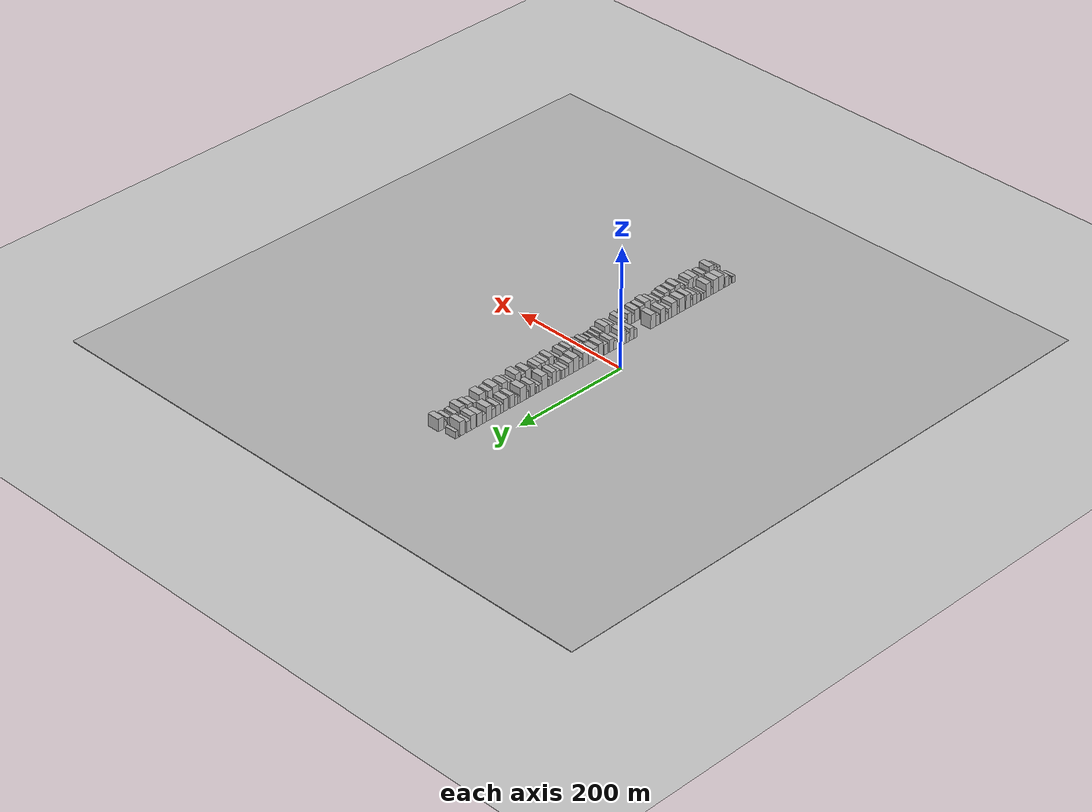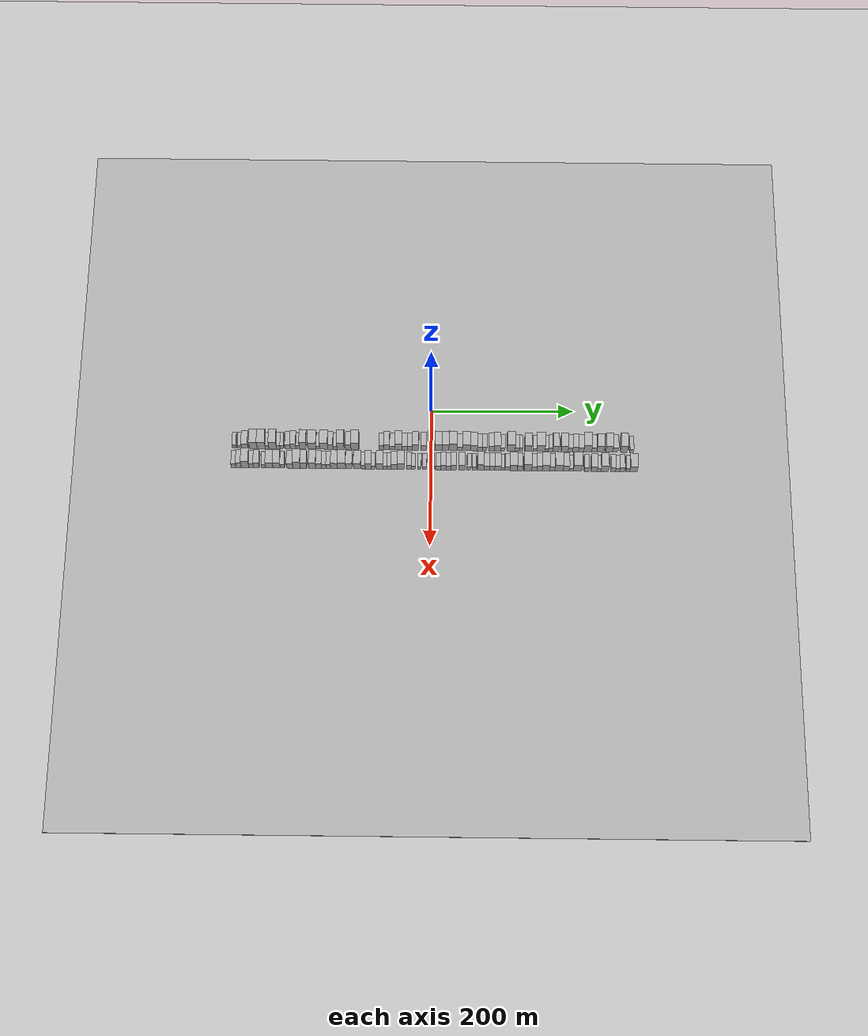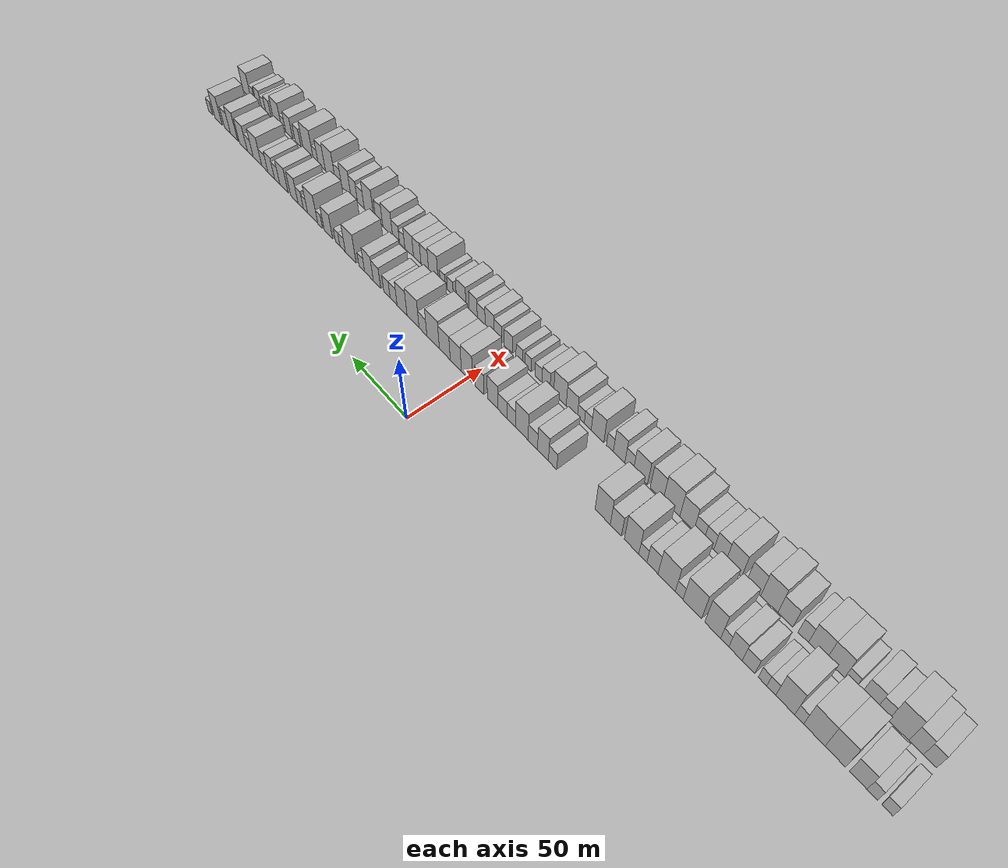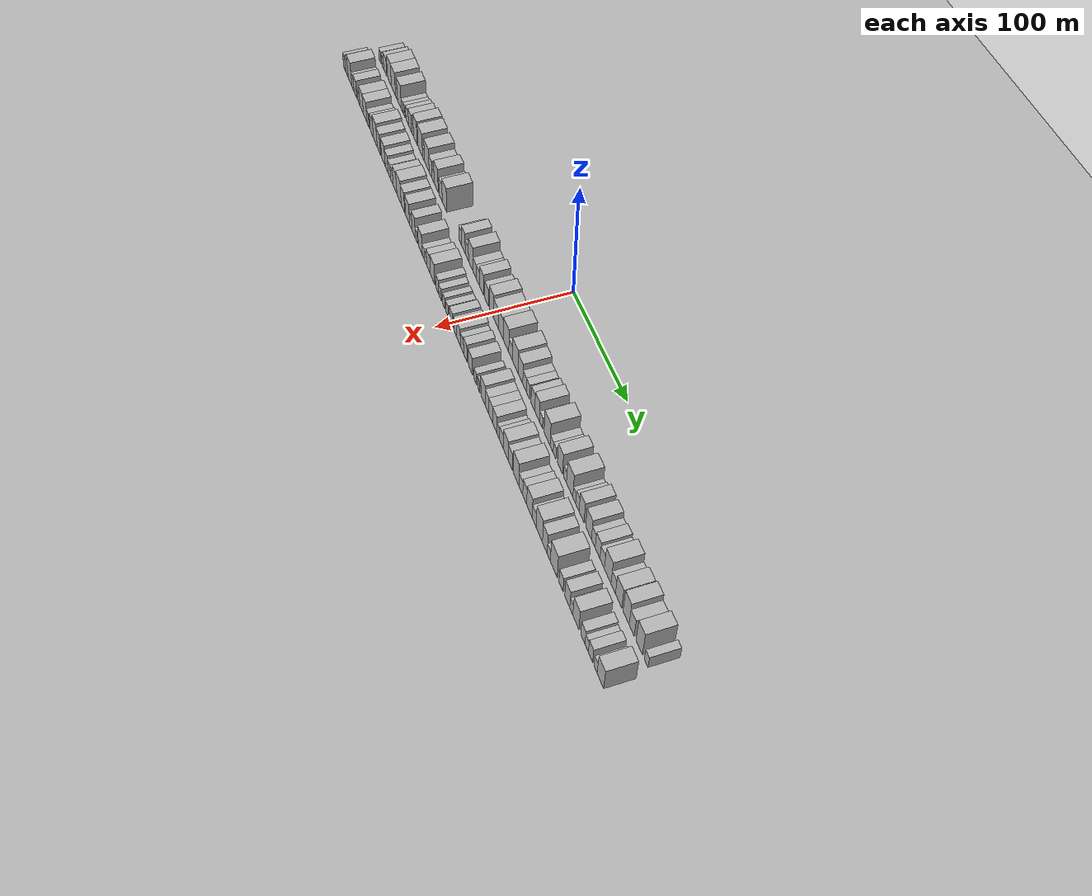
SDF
<?xml version="1.0" encoding="utf-8"?>

<sdf version="1.6">

   <world name="default">

      <gui fullscreen="0">

         <camera name="user_camera">

            <pose>-15 0 4.57585 0 0 0</pose>

            <view_controller>orbit</view_controller>

         </camera>

      </gui>

      <scene>

         <sky>

           <clouds>

             <speed>12</speed>

           </clouds>

         </sky>

         <ambient>0.4 0.4 0.4 1</ambient>

         <background>0.7 0.7 0.7 1</background>

         <shadows>1</shadows>

      </scene>

      <gravity>0 0 -9.8066</gravity>

      <magnetic_field>6e-06 2.3e-05 -4.2e-05</magnetic_field>

      <physics default="0" name="default_physics" type="ode">

         <ode>

            <solver>

               <type>quick</type>

               <iters>10</iters>

               <sor>1.0</sor>

               <use_dynamic_moi_rescaling>0</use_dynamic_moi_rescaling>

            </solver>

            <constraints>

               <cfm>0</cfm>

               <erp>0.2</erp>

               <contact_max_correcting_vel>100</contact_max_correcting_vel>

               <contact_surface_layer>0.001</contact_surface_layer>

            </constraints>

         </ode>

         <max_step_size>0.004</max_step_size>

         <real_time_factor>1</real_time_factor>

         <real_time_update_rate>250</real_time_update_rate>

      </physics>

      <light name="sun" type="directional">

         <cast_shadows>1</cast_shadows>

         <pose>0 0 10 0 0 0</pose>

         <diffuse>0.8 0.8 0.8 1</diffuse>

         <specular>0.2 0.2 0.2 1</specular>

         <attenuation>

            <range>1000</range>

            <constant>0.9</constant>

            <linear>0.01</linear>

            <quadratic>0.001</quadratic>

         </attenuation>

         <direction>-0.5 0.1 -0.9</direction>

      </light>

      <include>

         <name>ground_plane_1</name>

         <uri>model://HANNAS_ground_plane</uri>

         <pose>0 0 0  0 0 0</pose>

      </include>

      <include>

         <name>ground_plane_2</name>

         <uri>model://HANNAS_ground_plane</uri>

         <pose>100 0 0  0 0 0</pose>

      </include>

      <model name="building_1">

         <static>1</static>

         <pose frame="">50.0000 -275.2254 0 0.000000 0.000000 0.000000</pose>

         <link name="link">

            <pose frame="">0 0 6.00 0 0 0</pose>

            <collision name="collision">

               <geometry>

                  <box>

                     <size>20.0000 5.5493 12.0000</size>

                  </box>

               </geometry>

               <max_contacts>10</max_contacts>

               <surface>

                  <contact>

                     <ode/>

                  </contact>

                  <bounce/>

                  <friction>

                     <torsional>

                        <ode/>

                     </torsional>

                     <ode/>

                  </friction>

               </surface>

            </collision>

            <visual name="visual">

               <cast_shadows>0</cast_shadows>

               <geometry>

                  <box>

                     <size>20.0000 5.5493 12.0000</size>

                  </box>

               </geometry>

               <material>

                  <script>

                     <uri>model://HANNAS_wall/materials/scripts</uri>

                     <uri>model://HANNAS_wall/materials/textures</uri>

                     <name>vrc/HANNAS_wall</name>

                  </script>

               </material>

            </visual>

            <self_collide>0</self_collide>

            <enable_wind>0</enable_wind>

            <kinematic>0</kinematic>

         </link>

      </model>

      <model name="building_2">

         <static>1</static>

         <pose frame="">50.0000 -267.8029 0 0.000000 0.000000 0.000000</pose>

         <link name="link">

            <pose frame="">0 0 6.00 0 0 0</pose>

            <collision name="collision">

               <geometry>

                  <box>

                     <size>20.0000 5.2957 12.0000</size>

                  </box>

               </geometry>

               <max_contacts>10</max_contacts>

               <surface>

                  <contact>

                     <ode/>

                  </contact>

                  <bounce/>

                  <friction>

                     <torsional>

                        <ode/>

                     </torsional>

                     <ode/>

                  </friction>

               </surface>

            </collision>

            <visual name="visual">

               <cast_shadows>0</cast_shadows>

               <geometry>

                  <box>

                     <size>20.0000 5.2957 12.0000</size>

                  </box>

               </geometry>

               <material>

                  <script>

                     <uri>model://HANNAS_wall/materials/scripts</uri>

                     <uri>model://HANNAS_wall/materials/textures</uri>

                     <name>vrc/HANNAS_wall</name>

                  </script>

               </material>

            </visual>

            <self_collide>0</self_collide>

            <enable_wind>0</enable_wind>

            <kinematic>0</kinematic>

         </link>

      </model>

      <model name="building_3">

         <static>1</static>

         <pose frame="">50.0000 -260.6596 0 0.000000 0.000000 0.000000</pose>

         <link name="link">

            <pose frame="">0 0 9.00 0 0 0</pose>

            <collision name="collision">

               <geometry>

                  <box>

                     <size>20.0000 8.9908 18.0000</size>

                  </box>

               </geometry>

               <max_contacts>10</max_contacts>

               <surface>

                  <contact>

                     <ode/>

                  </contact>

                  <bounce/>

                  <friction>

                     <torsional>

                        <ode/>

                     </torsional>

                     <ode/>

                  </friction>

               </surface>

            </collision>

            <visual name="visual">

               <cast_shadows>0</cast_shadows>

               <geometry>

                  <box>

                     <size>20.0000 8.9908 18.0000</size>

                  </box>

               </geometry>

               <material>

                  <script>

                     <uri>model://HANNAS_wall/materials/scripts</uri>

                     <uri>model://HANNAS_wall/materials/textures</uri>

                     <name>vrc/HANNAS_wall</name>

                  </script>

               </material>

            </visual>

            <self_collide>0</self_collide>

            <enable_wind>0</enable_wind>

            <kinematic>0</kinematic>

         </link>

      </model>

      <model name="building_4">

         <static>1</static>

         <pose frame="">50.0000 -248.7745 0 0.000000 0.000000 0.000000</pose>

         <link name="link">

            <pose frame="">0 0 12.00 0 0 0</pose>

            <collision name="collision">

               <geometry>

                  <box>

                     <size>20.0000 10.7793 24.0000</size>

                  </box>

               </geometry>

               <max_contacts>10</max_contacts>

               <surface>

                  <contact>

                     <ode/>

                  </contact>

                  <bounce/>

                  <friction>

                     <torsional>

                        <ode/>

                     </torsional>

                     <ode/>

                  </friction>

               </surface>

            </collision>

            <visual name="visual">

               <cast_shadows>0</cast_shadows>

               <geometry>

                  <box>

                     <size>20.0000 10.7793 24.0000</size>

                  </box>

               </geometry>

               <material>

                  <script>

                     <uri>model://HANNAS_wall/materials/scripts</uri>

                     <uri>model://HANNAS_wall/materials/textures</uri>

                     <name>vrc/HANNAS_wall</name>

                  </script>

               </material>

            </visual>

            <self_collide>0</self_collide>

            <enable_wind>0</enable_wind>

            <kinematic>0</kinematic>

         </link>

      </model>

      <model name="building_5">

         <static>1</static>

         <pose frame="">50.0000 -237.6013 0 0.000000 0.000000 0.000000</pose>

         <link name="link">

            <pose frame="">0 0 12.00 0 0 0</pose>

            <collision name="collision">

               <geometry>

                  <box>

                     <size>20.0000 11.5671 24.0000</size>

                  </box>

               </geometry>

               <max_contacts>10</max_contacts>

               <surface>

                  <contact>

                     <ode/>

                  </contact>

                  <bounce/>

                  <friction>

                     <torsional>

                        <ode/>

                     </torsional>

                     <ode/>

                  </friction>

               </surface>

            </collision>

            <visual name="visual">

               <cast_shadows>0</cast_shadows>

               <geometry>

                  <box>

                     <size>20.0000 11.5671 24.0000</size>

                  </box>

               </geometry>

               <material>

                  <script>

                     <uri>model://HANNAS_wall/materials/scripts</uri>

                     <uri>model://HANNAS_wall/materials/textures</uri>

                     <name>vrc/HANNAS_wall</name>

                  </script>

               </material>

            </visual>

            <self_collide>0</self_collide>

            <enable_wind>0</enable_wind>

            <kinematic>0</kinematic>

         </link>

      </model>

      <model name="building_6">

         <static>1</static>

         <pose frame="">50.0000 -229.3475 0 0.000000 0.000000 0.000000</pose>

         <link name="link">

            <pose frame="">0 0 6.00 0 0 0</pose>

            <collision name="collision">

               <geometry>

                  <box>

                     <size>20.0000 4.9405 12.0000</size>

                  </box>

               </geometry>

               <max_contacts>10</max_contacts>

               <surface>

                  <contact>

                     <ode/>

                  </contact>

                  <bounce/>

                  <friction>

                     <torsional>

                        <ode/>

                     </torsional>

                     <ode/>

                  </friction>

               </surface>

            </collision>

            <visual name="visual">

               <cast_shadows>0</cast_shadows>

               <geometry>

                  <box>

                     <size>20.0000 4.9405 12.0000</size>

                  </box>

               </geometry>

               <material>

                  <script>

                     <uri>model://HANNAS_wall/materials/scripts</uri>

                     <uri>model://HANNAS_wall/materials/textures</uri>

                     <name>vrc/HANNAS_wall</name>

                  </script>

               </material>

            </visual>

            <self_collide>0</self_collide>

            <enable_wind>0</enable_wind>

            <kinematic>0</kinematic>

         </link>

      </model>

      <model name="building_7">

         <static>1</static>

         <pose frame="">50.0000 -221.5886 0 0.000000 0.000000 0.000000</pose>

         <link name="link">

            <pose frame="">0 0 12.00 0 0 0</pose>

            <collision name="collision">

               <geometry>

                  <box>

                     <size>20.0000 10.5772 24.0000</size>

                  </box>

               </geometry>

               <max_contacts>10</max_contacts>

               <surface>

                  <contact>

                     <ode/>

                  </contact>

                  <bounce/>

                  <friction>

                     <torsional>

                        <ode/>

                     </torsional>

                     <ode/>

                  </friction>

               </surface>

            </collision>

            <visual name="visual">

               <cast_shadows>0</cast_shadows>

               <geometry>

                  <box>

                     <size>20.0000 10.5772 24.0000</size>

                  </box>

               </geometry>

               <material>

                  <script>

                     <uri>model://HANNAS_wall/materials/scripts</uri>

                     <uri>model://HANNAS_wall/materials/textures</uri>

                     <name>vrc/HANNAS_wall</name>

                  </script>

               </material>

            </visual>

            <self_collide>0</self_collide>

            <enable_wind>0</enable_wind>

            <kinematic>0</kinematic>

         </link>

      </model>

      <model name="building_8">

         <static>1</static>

         <pose frame="">50.0000 -213.7445 0 0.000000 0.000000 0.000000</pose>

         <link name="link">

            <pose frame="">0 0 6.00 0 0 0</pose>

            <collision name="collision">

               <geometry>

                  <box>

                     <size>20.0000 5.1109 12.0000</size>

                  </box>

               </geometry>

               <max_contacts>10</max_contacts>

               <surface>

                  <contact>

                     <ode/>

                  </contact>

                  <bounce/>

                  <friction>

                     <torsional>

                        <ode/>

                     </torsional>

                     <ode/>

                  </friction>

               </surface>

            </collision>

            <visual name="visual">

               <cast_shadows>0</cast_shadows>

               <geometry>

                  <box>

                     <size>20.0000 5.1109 12.0000</size>

                  </box>

               </geometry>

               <material>

                  <script>

                     <uri>model://HANNAS_wall/materials/scripts</uri>

                     <uri>model://HANNAS_wall/materials/textures</uri>

                     <name>vrc/HANNAS_wall</name>

                  </script>

               </material>

            </visual>

            <self_collide>0</self_collide>

            <enable_wind>0</enable_wind>

            <kinematic>0</kinematic>

         </link>

      </model>

      <model name="building_9">

         <static>1</static>

         <pose frame="">50.0000 -208.7607 0 0.000000 0.000000 0.000000</pose>

         <link name="link">

            <pose frame="">0 0 6.00 0 0 0</pose>

            <collision name="collision">

               <geometry>

                  <box>

                     <size>20.0000 4.8567 12.0000</size>

                  </box>

               </geometry>

               <max_contacts>10</max_contacts>

               <surface>

                  <contact>

                     <ode/>

                  </contact>

                  <bounce/>

                  <friction>

                     <torsional>

                        <ode/>

                     </torsional>

                     <ode/>

                  </friction>

               </surface>

            </collision>

            <visual name="visual">

               <cast_shadows>0</cast_shadows>

               <geometry>

                  <box>

                     <size>20.0000 4.8567 12.0000</size>

                  </box>

               </geometry>

               <material>

                  <script>

                     <uri>model://HANNAS_wall/materials/scripts</uri>

                     <uri>model://HANNAS_wall/materials/textures</uri>

                     <name>vrc/HANNAS_wall</name>

                  </script>

               </material>

            </visual>

            <self_collide>0</self_collide>

            <enable_wind>0</enable_wind>

            <kinematic>0</kinematic>

         </link>

      </model>

      <model name="building_10">

         <static>1</static>

         <pose frame="">50.0000 -200.6562 0 0.000000 0.000000 0.000000</pose>

         <link name="link">

            <pose frame="">0 0 7.50 0 0 0</pose>

            <collision name="collision">

               <geometry>

                  <box>

                     <size>20.0000 7.3524 15.0000</size>

                  </box>

               </geometry>

               <max_contacts>10</max_contacts>

               <surface>

                  <contact>

                     <ode/>

                  </contact>

                  <bounce/>

                  <friction>

                     <torsional>

                        <ode/>

                     </torsional>

                     <ode/>

                  </friction>

               </surface>

            </collision>

            <visual name="visual">

               <cast_shadows>0</cast_shadows>

               <geometry>

                  <box>

                     <size>20.0000 7.3524 15.0000</size>

                  </box>

               </geometry>

               <material>

                  <script>

                     <uri>model://HANNAS_wall/materials/scripts</uri>

                     <uri>model://HANNAS_wall/materials/textures</uri>

                     <name>vrc/HANNAS_wall</name>

                  </script>

               </material>

            </visual>

            <self_collide>0</self_collide>

            <enable_wind>0</enable_wind>

            <kinematic>0</kinematic>

         </link>

      </model>

      <model name="building_11">

         <static>1</static>

         <pose frame="">50.0000 -192.9936 0 0.000000 0.000000 0.000000</pose>

         <link name="link">

            <pose frame="">0 0 9.00 0 0 0</pose>

            <collision name="collision">

               <geometry>

                  <box>

                     <size>20.0000 7.9729 18.0000</size>

                  </box>

               </geometry>

               <max_contacts>10</max_contacts>

               <surface>

                  <contact>

                     <ode/>

                  </contact>

                  <bounce/>

                  <friction>

                     <torsional>

                        <ode/>

                     </torsional>

                     <ode/>

                  </friction>

               </surface>

            </collision>

            <visual name="visual">

               <cast_shadows>0</cast_shadows>

               <geometry>

                  <box>

                     <size>20.0000 7.9729 18.0000</size>

                  </box>

               </geometry>

               <material>

                  <script>

                     <uri>model://HANNAS_wall/materials/scripts</uri>

                     <uri>model://HANNAS_wall/materials/textures</uri>

                     <name>vrc/HANNAS_wall</name>

                  </script>

               </material>

            </visual>

            <self_collide>0</self_collide>

            <enable_wind>0</enable_wind>

            <kinematic>0</kinematic>

         </link>

      </model>

      <model name="building_12">

         <static>1</static>

         <pose frame="">50.0000 -186.5411 0 0.000000 0.000000 0.000000</pose>

         <link name="link">

            <pose frame="">0 0 6.00 0 0 0</pose>

            <collision name="collision">

               <geometry>

                  <box>

                     <size>20.0000 4.9321 12.0000</size>

                  </box>

               </geometry>

               <max_contacts>10</max_contacts>

               <surface>

                  <contact>

                     <ode/>

                  </contact>

                  <bounce/>

                  <friction>

                     <torsional>

                        <ode/>

                     </torsional>

                     <ode/>

                  </friction>

               </surface>

            </collision>

            <visual name="visual">

               <cast_shadows>0</cast_shadows>

               <geometry>

                  <box>

                     <size>20.0000 4.9321 12.0000</size>

                  </box>

               </geometry>

               <material>

                  <script>

                     <uri>model://HANNAS_wall/materials/scripts</uri>

                     <uri>model://HANNAS_wall/materials/textures</uri>

                     <name>vrc/HANNAS_wall</name>

                  </script>

               </material>

            </visual>

            <self_collide>0</self_collide>

            <enable_wind>0</enable_wind>

            <kinematic>0</kinematic>

         </link>

      </model>

      <model name="building_13">

         <static>1</static>

         <pose frame="">50.0000 -179.2054 0 0.000000 0.000000 0.000000</pose>

         <link name="link">

            <pose frame="">0 0 12.00 0 0 0</pose>

            <collision name="collision">

               <geometry>

                  <box>

                     <size>20.0000 9.7393 24.0000</size>

                  </box>

               </geometry>

               <max_contacts>10</max_contacts>

               <surface>

                  <contact>

                     <ode/>

                  </contact>

                  <bounce/>

                  <friction>

                     <torsional>

                        <ode/>

                     </torsional>

                     <ode/>

                  </friction>

               </surface>

            </collision>

            <visual name="visual">

               <cast_shadows>0</cast_shadows>

               <geometry>

                  <box>

                     <size>20.0000 9.7393 24.0000</size>

                  </box>

               </geometry>

               <material>

                  <script>

                     <uri>model://HANNAS_wall/materials/scripts</uri>

                     <uri>model://HANNAS_wall/materials/textures</uri>

                     <name>vrc/HANNAS_wall</name>

                  </script>

               </material>

            </visual>

            <self_collide>0</self_collide>

            <enable_wind>0</enable_wind>

            <kinematic>0</kinematic>

         </link>

      </model>

      <model name="building_14">

         <static>1</static>

         <pose frame="">50.0000 -166.5232 0 0.000000 0.000000 0.000000</pose>

         <link name="link">

            <pose frame="">0 0 12.00 0 0 0</pose>

            <collision name="collision">

               <geometry>

                  <box>

                     <size>20.0000 11.6252 24.0000</size>

                  </box>

               </geometry>

               <max_contacts>10</max_contacts>

               <surface>

                  <contact>

                     <ode/>

                  </contact>

                  <bounce/>

                  <friction>

                     <torsional>

                        <ode/>

                     </torsional>

                     <ode/>

                  </friction>

               </surface>

            </collision>

            <visual name="visual">

               <cast_shadows>0</cast_shadows>

               <geometry>

                  <box>

                     <size>20.0000 11.6252 24.0000</size>

                  </box>

               </geometry>

               <material>

                  <script>

                     <uri>model://HANNAS_wall/materials/scripts</uri>

                     <uri>model://HANNAS_wall/materials/textures</uri>

                     <name>vrc/HANNAS_wall</name>

                  </script>

               </material>

            </visual>

            <self_collide>0</self_collide>

            <enable_wind>0</enable_wind>

            <kinematic>0</kinematic>

         </link>

      </model>

      <model name="building_15">

         <static>1</static>

         <pose frame="">50.0000 -158.1956 0 0.000000 0.000000 0.000000</pose>

         <link name="link">

            <pose frame="">0 0 6.00 0 0 0</pose>

            <collision name="collision">

               <geometry>

                  <box>

                     <size>20.0000 5.0300 12.0000</size>

                  </box>

               </geometry>

               <max_contacts>10</max_contacts>

               <surface>

                  <contact>

                     <ode/>

                  </contact>

                  <bounce/>

                  <friction>

                     <torsional>

                        <ode/>

                     </torsional>

                     <ode/>

                  </friction>

               </surface>

            </collision>

            <visual name="visual">

               <cast_shadows>0</cast_shadows>

               <geometry>

                  <box>

                     <size>20.0000 5.0300 12.0000</size>

                  </box>

               </geometry>

               <material>

                  <script>

                     <uri>model://HANNAS_wall/materials/scripts</uri>

                     <uri>model://HANNAS_wall/materials/textures</uri>

                     <name>vrc/HANNAS_wall</name>

                  </script>

               </material>

            </visual>

            <self_collide>0</self_collide>

            <enable_wind>0</enable_wind>

            <kinematic>0</kinematic>

         </link>

      </model>

      <model name="building_16">

         <static>1</static>

         <pose frame="">50.0000 -150.0507 0 0.000000 0.000000 0.000000</pose>

         <link name="link">

            <pose frame="">0 0 12.00 0 0 0</pose>

            <collision name="collision">

               <geometry>

                  <box>

                     <size>20.0000 11.2597 24.0000</size>

                  </box>

               </geometry>

               <max_contacts>10</max_contacts>

               <surface>

                  <contact>

                     <ode/>

                  </contact>

                  <bounce/>

                  <friction>

                     <torsional>

                        <ode/>

                     </torsional>

                     <ode/>

                  </friction>

               </surface>

            </collision>

            <visual name="visual">

               <cast_shadows>0</cast_shadows>

               <geometry>

                  <box>

                     <size>20.0000 11.2597 24.0000</size>

                  </box>

               </geometry>

               <material>

                  <script>

                     <uri>model://HANNAS_wall/materials/scripts</uri>

                     <uri>model://HANNAS_wall/materials/textures</uri>

                     <name>vrc/HANNAS_wall</name>

                  </script>

               </material>

            </visual>

            <self_collide>0</self_collide>

            <enable_wind>0</enable_wind>

            <kinematic>0</kinematic>

         </link>

      </model>

      <model name="building_17">

         <static>1</static>

         <pose frame="">50.0000 -140.7484 0 0.000000 0.000000 0.000000</pose>

         <link name="link">

            <pose frame="">0 0 9.00 0 0 0</pose>

            <collision name="collision">

               <geometry>

                  <box>

                     <size>20.0000 7.3451 18.0000</size>

                  </box>

               </geometry>

               <max_contacts>10</max_contacts>

               <surface>

                  <contact>

                     <ode/>

                  </contact>

                  <bounce/>

                  <friction>

                     <torsional>

                        <ode/>

                     </torsional>

                     <ode/>

                  </friction>

               </surface>

            </collision>

            <visual name="visual">

               <cast_shadows>0</cast_shadows>

               <geometry>

                  <box>

                     <size>20.0000 7.3451 18.0000</size>

                  </box>

               </geometry>

               <material>

                  <script>

                     <uri>model://HANNAS_wall/materials/scripts</uri>

                     <uri>model://HANNAS_wall/materials/textures</uri>

                     <name>vrc/HANNAS_wall</name>

                  </script>

               </material>

            </visual>

            <self_collide>0</self_collide>

            <enable_wind>0</enable_wind>

            <kinematic>0</kinematic>

         </link>

      </model>

      <model name="building_18">

         <static>1</static>

         <pose frame="">50.0000 -134.3213 0 0.000000 0.000000 0.000000</pose>

         <link name="link">

            <pose frame="">0 0 6.00 0 0 0</pose>

            <collision name="collision">

               <geometry>

                  <box>

                     <size>20.0000 5.5092 12.0000</size>

                  </box>

               </geometry>

               <max_contacts>10</max_contacts>

               <surface>

                  <contact>

                     <ode/>

                  </contact>

                  <bounce/>

                  <friction>

                     <torsional>

                        <ode/>

                     </torsional>

                     <ode/>

                  </friction>

               </surface>

            </collision>

            <visual name="visual">

               <cast_shadows>0</cast_shadows>

               <geometry>

                  <box>

                     <size>20.0000 5.5092 12.0000</size>

                  </box>

               </geometry>

               <material>

                  <script>

                     <uri>model://HANNAS_wall/materials/scripts</uri>

                     <uri>model://HANNAS_wall/materials/textures</uri>

                     <name>vrc/HANNAS_wall</name>

                  </script>

               </material>

            </visual>

            <self_collide>0</self_collide>

            <enable_wind>0</enable_wind>

            <kinematic>0</kinematic>

         </link>

      </model>

      <model name="building_19">

         <static>1</static>

         <pose frame="">50.0000 -126.6029 0 0.000000 0.000000 0.000000</pose>

         <link name="link">

            <pose frame="">0 0 12.00 0 0 0</pose>

            <collision name="collision">

               <geometry>

                  <box>

                     <size>20.0000 9.9276 24.0000</size>

                  </box>

               </geometry>

               <max_contacts>10</max_contacts>

               <surface>

                  <contact>

                     <ode/>

                  </contact>

                  <bounce/>

                  <friction>

                     <torsional>

                        <ode/>

                     </torsional>

                     <ode/>

                  </friction>

               </surface>

            </collision>

            <visual name="visual">

               <cast_shadows>0</cast_shadows>

               <geometry>

                  <box>

                     <size>20.0000 9.9276 24.0000</size>

                  </box>

               </geometry>

               <material>

                  <script>

                     <uri>model://HANNAS_wall/materials/scripts</uri>

                     <uri>model://HANNAS_wall/materials/textures</uri>

                     <name>vrc/HANNAS_wall</name>

                  </script>

               </material>

            </visual>

            <self_collide>0</self_collide>

            <enable_wind>0</enable_wind>

            <kinematic>0</kinematic>

         </link>

      </model>

      <model name="building_20">

         <static>1</static>

         <pose frame="">50.0000 -115.7636 0 0.000000 0.000000 0.000000</pose>

         <link name="link">

            <pose frame="">0 0 9.00 0 0 0</pose>

            <collision name="collision">

               <geometry>

                  <box>

                     <size>20.0000 7.7510 18.0000</size>

                  </box>

               </geometry>

               <max_contacts>10</max_contacts>

               <surface>

                  <contact>

                     <ode/>

                  </contact>

                  <bounce/>

                  <friction>

                     <torsional>

                        <ode/>

                     </torsional>

                     <ode/>

                  </friction>

               </surface>

            </collision>

            <visual name="visual">

               <cast_shadows>0</cast_shadows>

               <geometry>

                  <box>

                     <size>20.0000 7.7510 18.0000</size>

                  </box>

               </geometry>

               <material>

                  <script>

                     <uri>model://HANNAS_wall/materials/scripts</uri>

                     <uri>model://HANNAS_wall/materials/textures</uri>

                     <name>vrc/HANNAS_wall</name>

                  </script>

               </material>

            </visual>

            <self_collide>0</self_collide>

            <enable_wind>0</enable_wind>

            <kinematic>0</kinematic>

         </link>

      </model>

      <model name="building_21">

         <static>1</static>

         <pose frame="">50.0000 -106.4737 0 0.000000 0.000000 0.000000</pose>

         <link name="link">

            <pose frame="">0 0 12.00 0 0 0</pose>

            <collision name="collision">

               <geometry>

                  <box>

                     <size>20.0000 10.8287 24.0000</size>

                  </box>

               </geometry>

               <max_contacts>10</max_contacts>

               <surface>

                  <contact>

                     <ode/>

                  </contact>

                  <bounce/>

                  <friction>

                     <torsional>

                        <ode/>

                     </torsional>

                     <ode/>

                  </friction>

               </surface>

            </collision>

            <visual name="visual">

               <cast_shadows>0</cast_shadows>

               <geometry>

                  <box>

                     <size>20.0000 10.8287 24.0000</size>

                  </box>

               </geometry>

               <material>

                  <script>

                     <uri>model://HANNAS_wall/materials/scripts</uri>

                     <uri>model://HANNAS_wall/materials/textures</uri>

                     <name>vrc/HANNAS_wall</name>

                  </script>

               </material>

            </visual>

            <self_collide>0</self_collide>

            <enable_wind>0</enable_wind>

            <kinematic>0</kinematic>

         </link>

      </model>

      <model name="building_22">

         <static>1</static>

         <pose frame="">50.0000 -69.4700 0 0.000000 0.000000 0.000000</pose>

         <link name="link">

            <pose frame="">0 0 7.50 0 0 0</pose>

            <collision name="collision">

               <geometry>

                  <box>

                     <size>20.0000 6.3929 15.0000</size>

                  </box>

               </geometry>

               <max_contacts>10</max_contacts>

               <surface>

                  <contact>

                     <ode/>

                  </contact>

                  <bounce/>

                  <friction>

                     <torsional>

                        <ode/>

                     </torsional>

                     <ode/>

                  </friction>

               </surface>

            </collision>

            <visual name="visual">

               <cast_shadows>0</cast_shadows>

               <geometry>

                  <box>

                     <size>20.0000 6.3929 15.0000</size>

                  </box>

               </geometry>

               <material>

                  <script>

                     <uri>model://HANNAS_wall/materials/scripts</uri>

                     <uri>model://HANNAS_wall/materials/textures</uri>

                     <name>vrc/HANNAS_wall</name>

                  </script>

               </material>

            </visual>

            <self_collide>0</self_collide>

            <enable_wind>0</enable_wind>

            <kinematic>0</kinematic>

         </link>

      </model>

      <model name="building_23">

         <static>1</static>

         <pose frame="">50.0000 -62.0235 0 0.000000 0.000000 0.000000</pose>

         <link name="link">

            <pose frame="">0 0 10.50 0 0 0</pose>

            <collision name="collision">

               <geometry>

                  <box>

                     <size>20.0000 8.5001 21.0000</size>

                  </box>

               </geometry>

               <max_contacts>10</max_contacts>

               <surface>

                  <contact>

                     <ode/>

                  </contact>

                  <bounce/>

                  <friction>

                     <torsional>

                        <ode/>

                     </torsional>

                     <ode/>

                  </friction>

               </surface>

            </collision>

            <visual name="visual">

               <cast_shadows>0</cast_shadows>

               <geometry>

                  <box>

                     <size>20.0000 8.5001 21.0000</size>

                  </box>

               </geometry>

               <material>

                  <script>

                     <uri>model://HANNAS_wall/materials/scripts</uri>

                     <uri>model://HANNAS_wall/materials/textures</uri>

                     <name>vrc/HANNAS_wall</name>

                  </script>

               </material>

            </visual>

            <self_collide>0</self_collide>

            <enable_wind>0</enable_wind>

            <kinematic>0</kinematic>

         </link>

      </model>

      <model name="building_24">

         <static>1</static>

         <pose frame="">50.0000 -54.0751 0 0.000000 0.000000 0.000000</pose>

         <link name="link">

            <pose frame="">0 0 7.50 0 0 0</pose>

            <collision name="collision">

               <geometry>

                  <box>

                     <size>20.0000 7.3966 15.0000</size>

                  </box>

               </geometry>

               <max_contacts>10</max_contacts>

               <surface>

                  <contact>

                     <ode/>

                  </contact>

                  <bounce/>

                  <friction>

                     <torsional>

                        <ode/>

                     </torsional>

                     <ode/>

                  </friction>

               </surface>

            </collision>

            <visual name="visual">

               <cast_shadows>0</cast_shadows>

               <geometry>

                  <box>

                     <size>20.0000 7.3966 15.0000</size>

                  </box>

               </geometry>

               <material>

                  <script>

                     <uri>model://HANNAS_wall/materials/scripts</uri>

                     <uri>model://HANNAS_wall/materials/textures</uri>

                     <name>vrc/HANNAS_wall</name>

                  </script>

               </material>

            </visual>

            <self_collide>0</self_collide>

            <enable_wind>0</enable_wind>

            <kinematic>0</kinematic>

         </link>

      </model>

      <model name="building_25">

         <static>1</static>

         <pose frame="">50.0000 -45.3534 0 0.000000 0.000000 0.000000</pose>

         <link name="link">

            <pose frame="">0 0 12.00 0 0 0</pose>

            <collision name="collision">

               <geometry>

                  <box>

                     <size>20.0000 10.0468 24.0000</size>

                  </box>

               </geometry>

               <max_contacts>10</max_contacts>

               <surface>

                  <contact>

                     <ode/>

                  </contact>

                  <bounce/>

                  <friction>

                     <torsional>

                        <ode/>

                     </torsional>

                     <ode/>

                  </friction>

               </surface>

            </collision>

            <visual name="visual">

               <cast_shadows>0</cast_shadows>

               <geometry>

                  <box>

                     <size>20.0000 10.0468 24.0000</size>

                  </box>

               </geometry>

               <material>

                  <script>

                     <uri>model://HANNAS_wall/materials/scripts</uri>

                     <uri>model://HANNAS_wall/materials/textures</uri>

                     <name>vrc/HANNAS_wall</name>

                  </script>

               </material>

            </visual>

            <self_collide>0</self_collide>

            <enable_wind>0</enable_wind>

            <kinematic>0</kinematic>

         </link>

      </model>

      <model name="building_26">

         <static>1</static>

         <pose frame="">50.0000 -36.7470 0 0.000000 0.000000 0.000000</pose>

         <link name="link">

            <pose frame="">0 0 7.50 0 0 0</pose>

            <collision name="collision">

               <geometry>

                  <box>

                     <size>20.0000 7.1660 15.0000</size>

                  </box>

               </geometry>

               <max_contacts>10</max_contacts>

               <surface>

                  <contact>

                     <ode/>

                  </contact>

                  <bounce/>

                  <friction>

                     <torsional>

                        <ode/>

                     </torsional>

                     <ode/>

                  </friction>

               </surface>

            </collision>

            <visual name="visual">

               <cast_shadows>0</cast_shadows>

               <geometry>

                  <box>

                     <size>20.0000 7.1660 15.0000</size>

                  </box>

               </geometry>

               <material>

                  <script>

                     <uri>model://HANNAS_wall/materials/scripts</uri>

                     <uri>model://HANNAS_wall/materials/textures</uri>

                     <name>vrc/HANNAS_wall</name>

                  </script>

               </material>

            </visual>

            <self_collide>0</self_collide>

            <enable_wind>0</enable_wind>

            <kinematic>0</kinematic>

         </link>

      </model>

      <model name="building_27">

         <static>1</static>

         <pose frame="">50.0000 -29.4997 0 0.000000 0.000000 0.000000</pose>

         <link name="link">

            <pose frame="">0 0 7.50 0 0 0</pose>

            <collision name="collision">

               <geometry>

                  <box>

                     <size>20.0000 7.3286 15.0000</size>

                  </box>

               </geometry>

               <max_contacts>10</max_contacts>

               <surface>

                  <contact>

                     <ode/>

                  </contact>

                  <bounce/>

                  <friction>

                     <torsional>

                        <ode/>

                     </torsional>

                     <ode/>

                  </friction>

               </surface>

            </collision>

            <visual name="visual">

               <cast_shadows>0</cast_shadows>

               <geometry>

                  <box>

                     <size>20.0000 7.3286 15.0000</size>

                  </box>

               </geometry>

               <material>

                  <script>

                     <uri>model://HANNAS_wall/materials/scripts</uri>

                     <uri>model://HANNAS_wall/materials/textures</uri>

                     <name>vrc/HANNAS_wall</name>

                  </script>

               </material>

            </visual>

            <self_collide>0</self_collide>

            <enable_wind>0</enable_wind>

            <kinematic>0</kinematic>

         </link>

      </model>

      <model name="building_28">

         <static>1</static>

         <pose frame="">50.0000 -21.4595 0 0.000000 0.000000 0.000000</pose>

         <link name="link">

            <pose frame="">0 0 10.50 0 0 0</pose>

            <collision name="collision">

               <geometry>

                  <box>

                     <size>20.0000 8.7516 21.0000</size>

                  </box>

               </geometry>

               <max_contacts>10</max_contacts>

               <surface>

                  <contact>

                     <ode/>

                  </contact>

                  <bounce/>

                  <friction>

                     <torsional>

                        <ode/>

                     </torsional>

                     <ode/>

                  </friction>

               </surface>

            </collision>

            <visual name="visual">

               <cast_shadows>0</cast_shadows>

               <geometry>

                  <box>

                     <size>20.0000 8.7516 21.0000</size>

                  </box>

               </geometry>

               <material>

                  <script>

                     <uri>model://HANNAS_wall/materials/scripts</uri>

                     <uri>model://HANNAS_wall/materials/textures</uri>

                     <name>vrc/HANNAS_wall</name>

                  </script>

               </material>

            </visual>

            <self_collide>0</self_collide>

            <enable_wind>0</enable_wind>

            <kinematic>0</kinematic>

         </link>

      </model>

      <model name="building_29">

         <static>1</static>

         <pose frame="">50.0000 -10.2537 0 0.000000 0.000000 0.000000</pose>

         <link name="link">

            <pose frame="">0 0 9.00 0 0 0</pose>

            <collision name="collision">

               <geometry>

                  <box>

                     <size>20.0000 7.6600 18.0000</size>

                  </box>

               </geometry>

               <max_contacts>10</max_contacts>

               <surface>

                  <contact>

                     <ode/>

                  </contact>

                  <bounce/>

                  <friction>

                     <torsional>

                        <ode/>

                     </torsional>

                     <ode/>

                  </friction>

               </surface>

            </collision>

            <visual name="visual">

               <cast_shadows>0</cast_shadows>

               <geometry>

                  <box>

                     <size>20.0000 7.6600 18.0000</size>

                  </box>

               </geometry>

               <material>

                  <script>

                     <uri>model://HANNAS_wall/materials/scripts</uri>

                     <uri>model://HANNAS_wall/materials/textures</uri>

                     <name>vrc/HANNAS_wall</name>

                  </script>

               </material>

            </visual>

            <self_collide>0</self_collide>

            <enable_wind>0</enable_wind>

            <kinematic>0</kinematic>

         </link>

      </model>

      <model name="building_30">

         <static>1</static>

         <pose frame="">50.0000 0.4802 0 0.000000 0.000000 0.000000</pose>

         <link name="link">

            <pose frame="">0 0 12.00 0 0 0</pose>

            <collision name="collision">

               <geometry>

                  <box>

                     <size>20.0000 9.8076 24.0000</size>

                  </box>

               </geometry>

               <max_contacts>10</max_contacts>

               <surface>

                  <contact>

                     <ode/>

                  </contact>

                  <bounce/>

                  <friction>

                     <torsional>

                        <ode/>

                     </torsional>

                     <ode/>

                  </friction>

               </surface>

            </collision>

            <visual name="visual">

               <cast_shadows>0</cast_shadows>

               <geometry>

                  <box>

                     <size>20.0000 9.8076 24.0000</size>

                  </box>

               </geometry>

               <material>

                  <script>

                     <uri>model://HANNAS_wall/materials/scripts</uri>

                     <uri>model://HANNAS_wall/materials/textures</uri>

                     <name>vrc/HANNAS_wall</name>

                  </script>

               </material>

            </visual>

            <self_collide>0</self_collide>

            <enable_wind>0</enable_wind>

            <kinematic>0</kinematic>

         </link>

      </model>

      <model name="building_31">

         <static>1</static>

         <pose frame="">50.0000 10.3010 0 0.000000 0.000000 0.000000</pose>

         <link name="link">

            <pose frame="">0 0 10.50 0 0 0</pose>

            <collision name="collision">

               <geometry>

                  <box>

                     <size>20.0000 9.8340 21.0000</size>

                  </box>

               </geometry>

               <max_contacts>10</max_contacts>

               <surface>

                  <contact>

                     <ode/>

                  </contact>

                  <bounce/>

                  <friction>

                     <torsional>

                        <ode/>

                     </torsional>

                     <ode/>

                  </friction>

               </surface>

            </collision>

            <visual name="visual">

               <cast_shadows>0</cast_shadows>

               <geometry>

                  <box>

                     <size>20.0000 9.8340 21.0000</size>

                  </box>

               </geometry>

               <material>

                  <script>

                     <uri>model://HANNAS_wall/materials/scripts</uri>

                     <uri>model://HANNAS_wall/materials/textures</uri>

                     <name>vrc/HANNAS_wall</name>

                  </script>

               </material>

            </visual>

            <self_collide>0</self_collide>

            <enable_wind>0</enable_wind>

            <kinematic>0</kinematic>

         </link>

      </model>

      <model name="building_32">

         <static>1</static>

         <pose frame="">50.0000 20.1373 0 0.000000 0.000000 0.000000</pose>

         <link name="link">

            <pose frame="">0 0 10.50 0 0 0</pose>

            <collision name="collision">

               <geometry>

                  <box>

                     <size>20.0000 9.8388 21.0000</size>

                  </box>

               </geometry>

               <max_contacts>10</max_contacts>

               <surface>

                  <contact>

                     <ode/>

                  </contact>

                  <bounce/>

                  <friction>

                     <torsional>

                        <ode/>

                     </torsional>

                     <ode/>

                  </friction>

               </surface>

            </collision>

            <visual name="visual">

               <cast_shadows>0</cast_shadows>

               <geometry>

                  <box>

                     <size>20.0000 9.8388 21.0000</size>

                  </box>

               </geometry>

               <material>

                  <script>

                     <uri>model://HANNAS_wall/materials/scripts</uri>

                     <uri>model://HANNAS_wall/materials/textures</uri>

                     <name>vrc/HANNAS_wall</name>

                  </script>

               </material>

            </visual>

            <self_collide>0</self_collide>

            <enable_wind>0</enable_wind>

            <kinematic>0</kinematic>

         </link>

      </model>

      <model name="building_33">

         <static>1</static>

         <pose frame="">50.0000 30.8102 0 0.000000 0.000000 0.000000</pose>

         <link name="link">

            <pose frame="">0 0 12.00 0 0 0</pose>

            <collision name="collision">

               <geometry>

                  <box>

                     <size>20.0000 11.5070 24.0000</size>

                  </box>

               </geometry>

               <max_contacts>10</max_contacts>

               <surface>

                  <contact>

                     <ode/>

                  </contact>

                  <bounce/>

                  <friction>

                     <torsional>

                        <ode/>

                     </torsional>

                     <ode/>

                  </friction>

               </surface>

            </collision>

            <visual name="visual">

               <cast_shadows>0</cast_shadows>

               <geometry>

                  <box>

                     <size>20.0000 11.5070 24.0000</size>

                  </box>

               </geometry>

               <material>

                  <script>

                     <uri>model://HANNAS_wall/materials/scripts</uri>

                     <uri>model://HANNAS_wall/materials/textures</uri>

                     <name>vrc/HANNAS_wall</name>

                  </script>

               </material>

            </visual>

            <self_collide>0</self_collide>

            <enable_wind>0</enable_wind>

            <kinematic>0</kinematic>

         </link>

      </model>

      <model name="building_34">

         <static>1</static>

         <pose frame="">50.0000 40.2271 0 0.000000 0.000000 0.000000</pose>

         <link name="link">

            <pose frame="">0 0 7.50 0 0 0</pose>

            <collision name="collision">

               <geometry>

                  <box>

                     <size>20.0000 7.3268 15.0000</size>

                  </box>

               </geometry>

               <max_contacts>10</max_contacts>

               <surface>

                  <contact>

                     <ode/>

                  </contact>

                  <bounce/>

                  <friction>

                     <torsional>

                        <ode/>

                     </torsional>

                     <ode/>

                  </friction>

               </surface>

            </collision>

            <visual name="visual">

               <cast_shadows>0</cast_shadows>

               <geometry>

                  <box>

                     <size>20.0000 7.3268 15.0000</size>

                  </box>

               </geometry>

               <material>

                  <script>

                     <uri>model://HANNAS_wall/materials/scripts</uri>

                     <uri>model://HANNAS_wall/materials/textures</uri>

                     <name>vrc/HANNAS_wall</name>

                  </script>

               </material>

            </visual>

            <self_collide>0</self_collide>

            <enable_wind>0</enable_wind>

            <kinematic>0</kinematic>

         </link>

      </model>

      <model name="building_35">

         <static>1</static>

         <pose frame="">50.0000 49.6016 0 0.000000 0.000000 0.000000</pose>

         <link name="link">

            <pose frame="">0 0 12.00 0 0 0</pose>

            <collision name="collision">

               <geometry>

                  <box>

                     <size>20.0000 11.4222 24.0000</size>

                  </box>

               </geometry>

               <max_contacts>10</max_contacts>

               <surface>

                  <contact>

                     <ode/>

                  </contact>

                  <bounce/>

                  <friction>

                     <torsional>

                        <ode/>

                     </torsional>

                     <ode/>

                  </friction>

               </surface>

            </collision>

            <visual name="visual">

               <cast_shadows>0</cast_shadows>

               <geometry>

                  <box>

                     <size>20.0000 11.4222 24.0000</size>

                  </box>

               </geometry>

               <material>

                  <script>

                     <uri>model://HANNAS_wall/materials/scripts</uri>

                     <uri>model://HANNAS_wall/materials/textures</uri>

                     <name>vrc/HANNAS_wall</name>

                  </script>

               </material>

            </visual>

            <self_collide>0</self_collide>

            <enable_wind>0</enable_wind>

            <kinematic>0</kinematic>

         </link>

      </model>

      <model name="building_36">

         <static>1</static>

         <pose frame="">50.0000 60.0975 0 0.000000 0.000000 0.000000</pose>

         <link name="link">

            <pose frame="">0 0 10.50 0 0 0</pose>

            <collision name="collision">

               <geometry>

                  <box>

                     <size>20.0000 9.5696 21.0000</size>

                  </box>

               </geometry>

               <max_contacts>10</max_contacts>

               <surface>

                  <contact>

                     <ode/>

                  </contact>

                  <bounce/>

                  <friction>

                     <torsional>

                        <ode/>

                     </torsional>

                     <ode/>

                  </friction>

               </surface>

            </collision>

            <visual name="visual">

               <cast_shadows>0</cast_shadows>

               <geometry>

                  <box>

                     <size>20.0000 9.5696 21.0000</size>

                  </box>

               </geometry>

               <material>

                  <script>

                     <uri>model://HANNAS_wall/materials/scripts</uri>

                     <uri>model://HANNAS_wall/materials/textures</uri>

                     <name>vrc/HANNAS_wall</name>

                  </script>

               </material>

            </visual>

            <self_collide>0</self_collide>

            <enable_wind>0</enable_wind>

            <kinematic>0</kinematic>

         </link>

      </model>

      <model name="building_37">

         <static>1</static>

         <pose frame="">50.0000 68.3081 0 0.000000 0.000000 0.000000</pose>

         <link name="link">

            <pose frame="">0 0 7.50 0 0 0</pose>

            <collision name="collision">

               <geometry>

                  <box>

                     <size>20.0000 6.8517 15.0000</size>

                  </box>

               </geometry>

               <max_contacts>10</max_contacts>

               <surface>

                  <contact>

                     <ode/>

                  </contact>

                  <bounce/>

                  <friction>

                     <torsional>

                        <ode/>

                     </torsional>

                     <ode/>

                  </friction>

               </surface>

            </collision>

            <visual name="visual">

               <cast_shadows>0</cast_shadows>

               <geometry>

                  <box>

                     <size>20.0000 6.8517 15.0000</size>

                  </box>

               </geometry>

               <material>

                  <script>

                     <uri>model://HANNAS_wall/materials/scripts</uri>

                     <uri>model://HANNAS_wall/materials/textures</uri>

                     <name>vrc/HANNAS_wall</name>

                  </script>

               </material>

            </visual>

            <self_collide>0</self_collide>

            <enable_wind>0</enable_wind>

            <kinematic>0</kinematic>

         </link>

      </model>

      <model name="building_38">

         <static>1</static>

         <pose frame="">50.0000 74.9236 0 0.000000 0.000000 0.000000</pose>

         <link name="link">

            <pose frame="">0 0 7.50 0 0 0</pose>

            <collision name="collision">

               <geometry>

                  <box>

                     <size>20.0000 6.3793 15.0000</size>

                  </box>

               </geometry>

               <max_contacts>10</max_contacts>

               <surface>

                  <contact>

                     <ode/>

                  </contact>

                  <bounce/>

                  <friction>

                     <torsional>

                        <ode/>

                     </torsional>

                     <ode/>

                  </friction>

               </surface>

            </collision>

            <visual name="visual">

               <cast_shadows>0</cast_shadows>

               <geometry>

                  <box>

                     <size>20.0000 6.3793 15.0000</size>

                  </box>

               </geometry>

               <material>

                  <script>

                     <uri>model://HANNAS_wall/materials/scripts</uri>

                     <uri>model://HANNAS_wall/materials/textures</uri>

                     <name>vrc/HANNAS_wall</name>

                  </script>

               </material>

            </visual>

            <self_collide>0</self_collide>

            <enable_wind>0</enable_wind>

            <kinematic>0</kinematic>

         </link>

      </model>

      <model name="building_39">

         <static>1</static>

         <pose frame="">50.0000 84.8796 0 0.000000 0.000000 0.000000</pose>

         <link name="link">

            <pose frame="">0 0 9.00 0 0 0</pose>

            <collision name="collision">

               <geometry>

                  <box>

                     <size>20.0000 7.5326 18.0000</size>

                  </box>

               </geometry>

               <max_contacts>10</max_contacts>

               <surface>

                  <contact>

                     <ode/>

                  </contact>

                  <bounce/>

                  <friction>

                     <torsional>

                        <ode/>

                     </torsional>

                     <ode/>

                  </friction>

               </surface>

            </collision>

            <visual name="visual">

               <cast_shadows>0</cast_shadows>

               <geometry>

                  <box>

                     <size>20.0000 7.5326 18.0000</size>

                  </box>

               </geometry>

               <material>

                  <script>

                     <uri>model://HANNAS_wall/materials/scripts</uri>

                     <uri>model://HANNAS_wall/materials/textures</uri>

                     <name>vrc/HANNAS_wall</name>

                  </script>

               </material>

            </visual>

            <self_collide>0</self_collide>

            <enable_wind>0</enable_wind>

            <kinematic>0</kinematic>

         </link>

      </model>

      <model name="building_40">

         <static>1</static>

         <pose frame="">50.0000 93.0982 0 0.000000 0.000000 0.000000</pose>

         <link name="link">

            <pose frame="">0 0 10.50 0 0 0</pose>

            <collision name="collision">

               <geometry>

                  <box>

                     <size>20.0000 8.9047 21.0000</size>

                  </box>

               </geometry>

               <max_contacts>10</max_contacts>

               <surface>

                  <contact>

                     <ode/>

                  </contact>

                  <bounce/>

                  <friction>

                     <torsional>

                        <ode/>

                     </torsional>

                     <ode/>

                  </friction>

               </surface>

            </collision>

            <visual name="visual">

               <cast_shadows>0</cast_shadows>

               <geometry>

                  <box>

                     <size>20.0000 8.9047 21.0000</size>

                  </box>

               </geometry>

               <material>

                  <script>

                     <uri>model://HANNAS_wall/materials/scripts</uri>

                     <uri>model://HANNAS_wall/materials/textures</uri>

                     <name>vrc/HANNAS_wall</name>

                  </script>

               </material>

            </visual>

            <self_collide>0</self_collide>

            <enable_wind>0</enable_wind>

            <kinematic>0</kinematic>

         </link>

      </model>

      <model name="building_41">

         <static>1</static>

         <pose frame="">50.0000 100.4825 0 0.000000 0.000000 0.000000</pose>

         <link name="link">

            <pose frame="">0 0 6.00 0 0 0</pose>

            <collision name="collision">

               <geometry>

                  <box>

                     <size>20.0000 5.8639 12.0000</size>

                  </box>

               </geometry>

               <max_contacts>10</max_contacts>

               <surface>

                  <contact>

                     <ode/>

                  </contact>

                  <bounce/>

                  <friction>

                     <torsional>

                        <ode/>

                     </torsional>

                     <ode/>

                  </friction>

               </surface>

            </collision>

            <visual name="visual">

               <cast_shadows>0</cast_shadows>

               <geometry>

                  <box>

                     <size>20.0000 5.8639 12.0000</size>

                  </box>

               </geometry>

               <material>

                  <script>

                     <uri>model://HANNAS_wall/materials/scripts</uri>

                     <uri>model://HANNAS_wall/materials/textures</uri>

                     <name>vrc/HANNAS_wall</name>

                  </script>

               </material>

            </visual>

            <self_collide>0</self_collide>

            <enable_wind>0</enable_wind>

            <kinematic>0</kinematic>

         </link>

      </model>

      <model name="building_42">

         <static>1</static>

         <pose frame="">50.0000 112.0596 0 0.000000 0.000000 0.000000</pose>

         <link name="link">

            <pose frame="">0 0 12.00 0 0 0</pose>

            <collision name="collision">

               <geometry>

                  <box>

                     <size>20.0000 11.2903 24.0000</size>

                  </box>

               </geometry>

               <max_contacts>10</max_contacts>

               <surface>

                  <contact>

                     <ode/>

                  </contact>

                  <bounce/>

                  <friction>

                     <torsional>

                        <ode/>

                     </torsional>

                     <ode/>

                  </friction>

               </surface>

            </collision>

            <visual name="visual">

               <cast_shadows>0</cast_shadows>

               <geometry>

                  <box>

                     <size>20.0000 11.2903 24.0000</size>

                  </box>

               </geometry>

               <material>

                  <script>

                     <uri>model://HANNAS_wall/materials/scripts</uri>

                     <uri>model://HANNAS_wall/materials/textures</uri>

                     <name>vrc/HANNAS_wall</name>

                  </script>

               </material>

            </visual>

            <self_collide>0</self_collide>

            <enable_wind>0</enable_wind>

            <kinematic>0</kinematic>

         </link>

      </model>

      <model name="building_43">

         <static>1</static>

         <pose frame="">50.0000 120.6020 0 0.000000 0.000000 0.000000</pose>

         <link name="link">

            <pose frame="">0 0 6.00 0 0 0</pose>

            <collision name="collision">

               <geometry>

                  <box>

                     <size>20.0000 5.7946 12.0000</size>

                  </box>

               </geometry>

               <max_contacts>10</max_contacts>

               <surface>

                  <contact>

                     <ode/>

                  </contact>

                  <bounce/>

                  <friction>

                     <torsional>

                        <ode/>

                     </torsional>

                     <ode/>

                  </friction>

               </surface>

            </collision>

            <visual name="visual">

               <cast_shadows>0</cast_shadows>

               <geometry>

                  <box>

                     <size>20.0000 5.7946 12.0000</size>

                  </box>

               </geometry>

               <material>

                  <script>

                     <uri>model://HANNAS_wall/materials/scripts</uri>

                     <uri>model://HANNAS_wall/materials/textures</uri>

                     <name>vrc/HANNAS_wall</name>

                  </script>

               </material>

            </visual>

            <self_collide>0</self_collide>

            <enable_wind>0</enable_wind>

            <kinematic>0</kinematic>

         </link>

      </model>

      <model name="building_44">

         <static>1</static>

         <pose frame="">50.0000 125.9452 0 0.000000 0.000000 0.000000</pose>

         <link name="link">

            <pose frame="">0 0 6.00 0 0 0</pose>

            <collision name="collision">

               <geometry>

                  <box>

                     <size>20.0000 4.8918 12.0000</size>

                  </box>

               </geometry>

               <max_contacts>10</max_contacts>

               <surface>

                  <contact>

                     <ode/>

                  </contact>

                  <bounce/>

                  <friction>

                     <torsional>

                        <ode/>

                     </torsional>

                     <ode/>

                  </friction>

               </surface>

            </collision>

            <visual name="visual">

               <cast_shadows>0</cast_shadows>

               <geometry>

                  <box>

                     <size>20.0000 4.8918 12.0000</size>

                  </box>

               </geometry>

               <material>

                  <script>

                     <uri>model://HANNAS_wall/materials/scripts</uri>

                     <uri>model://HANNAS_wall/materials/textures</uri>

                     <name>vrc/HANNAS_wall</name>

                  </script>

               </material>

            </visual>

            <self_collide>0</self_collide>

            <enable_wind>0</enable_wind>

            <kinematic>0</kinematic>

         </link>

      </model>

      <model name="building_45">

         <static>1</static>

         <pose frame="">50.0000 136.0157 0 0.000000 0.000000 0.000000</pose>

         <link name="link">

            <pose frame="">0 0 10.50 0 0 0</pose>

            <collision name="collision">

               <geometry>

                  <box>

                     <size>20.0000 9.2492 21.0000</size>

                  </box>

               </geometry>

               <max_contacts>10</max_contacts>

               <surface>

                  <contact>

                     <ode/>

                  </contact>

                  <bounce/>

                  <friction>

                     <torsional>

                        <ode/>

                     </torsional>

                     <ode/>

                  </friction>

               </surface>

            </collision>

            <visual name="visual">

               <cast_shadows>0</cast_shadows>

               <geometry>

                  <box>

                     <size>20.0000 9.2492 21.0000</size>

                  </box>

               </geometry>

               <material>

                  <script>

                     <uri>model://HANNAS_wall/materials/scripts</uri>

                     <uri>model://HANNAS_wall/materials/textures</uri>

                     <name>vrc/HANNAS_wall</name>

                  </script>

               </material>

            </visual>

            <self_collide>0</self_collide>

            <enable_wind>0</enable_wind>

            <kinematic>0</kinematic>

         </link>

      </model>

      <model name="building_46">

         <static>1</static>

         <pose frame="">50.0000 145.2747 0 0.000000 0.000000 0.000000</pose>

         <link name="link">

            <pose frame="">0 0 6.00 0 0 0</pose>

            <collision name="collision">

               <geometry>

                  <box>

                     <size>20.0000 5.2688 12.0000</size>

                  </box>

               </geometry>

               <max_contacts>10</max_contacts>

               <surface>

                  <contact>

                     <ode/>

                  </contact>

                  <bounce/>

                  <friction>

                     <torsional>

                        <ode/>

                     </torsional>

                     <ode/>

                  </friction>

               </surface>

            </collision>

            <visual name="visual">

               <cast_shadows>0</cast_shadows>

               <geometry>

                  <box>

                     <size>20.0000 5.2688 12.0000</size>

                  </box>

               </geometry>

               <material>

                  <script>

                     <uri>model://HANNAS_wall/materials/scripts</uri>

                     <uri>model://HANNAS_wall/materials/textures</uri>

                     <name>vrc/HANNAS_wall</name>

                  </script>

               </material>

            </visual>

            <self_collide>0</self_collide>

            <enable_wind>0</enable_wind>

            <kinematic>0</kinematic>

         </link>

      </model>

      <model name="building_47">

         <static>1</static>

         <pose frame="">50.0000 153.6020 0 0.000000 0.000000 0.000000</pose>

         <link name="link">

            <pose frame="">0 0 12.00 0 0 0</pose>

            <collision name="collision">

               <geometry>

                  <box>

                     <size>20.0000 11.3859 24.0000</size>

                  </box>

               </geometry>

               <max_contacts>10</max_contacts>

               <surface>

                  <contact>

                     <ode/>

                  </contact>

                  <bounce/>

                  <friction>

                     <torsional>

                        <ode/>

                     </torsional>

                     <ode/>

                  </friction>

               </surface>

            </collision>

            <visual name="visual">

               <cast_shadows>0</cast_shadows>

               <geometry>

                  <box>

                     <size>20.0000 11.3859 24.0000</size>

                  </box>

               </geometry>

               <material>

                  <script>

                     <uri>model://HANNAS_wall/materials/scripts</uri>

                     <uri>model://HANNAS_wall/materials/textures</uri>

                     <name>vrc/HANNAS_wall</name>

                  </script>

               </material>

            </visual>

            <self_collide>0</self_collide>

            <enable_wind>0</enable_wind>

            <kinematic>0</kinematic>

         </link>

      </model>

      <model name="building_48">

         <static>1</static>

         <pose frame="">50.0000 161.7843 0 0.000000 0.000000 0.000000</pose>

         <link name="link">

            <pose frame="">0 0 6.00 0 0 0</pose>

            <collision name="collision">

               <geometry>

                  <box>

                     <size>20.0000 4.9787 12.0000</size>

                  </box>

               </geometry>

               <max_contacts>10</max_contacts>

               <surface>

                  <contact>

                     <ode/>

                  </contact>

                  <bounce/>

                  <friction>

                     <torsional>

                        <ode/>

                     </torsional>

                     <ode/>

                  </friction>

               </surface>

            </collision>

            <visual name="visual">

               <cast_shadows>0</cast_shadows>

               <geometry>

                  <box>

                     <size>20.0000 4.9787 12.0000</size>

                  </box>

               </geometry>

               <material>

                  <script>

                     <uri>model://HANNAS_wall/materials/scripts</uri>

                     <uri>model://HANNAS_wall/materials/textures</uri>

                     <name>vrc/HANNAS_wall</name>

                  </script>

               </material>

            </visual>

            <self_collide>0</self_collide>

            <enable_wind>0</enable_wind>

            <kinematic>0</kinematic>

         </link>

      </model>

      <model name="building_49">

         <static>1</static>

         <pose frame="">50.0000 167.3069 0 0.000000 0.000000 0.000000</pose>

         <link name="link">

            <pose frame="">0 0 7.50 0 0 0</pose>

            <collision name="collision">

               <geometry>

                  <box>

                     <size>20.0000 6.0666 15.0000</size>

                  </box>

               </geometry>

               <max_contacts>10</max_contacts>

               <surface>

                  <contact>

                     <ode/>

                  </contact>

                  <bounce/>

                  <friction>

                     <torsional>

                        <ode/>

                     </torsional>

                     <ode/>

                  </friction>

               </surface>

            </collision>

            <visual name="visual">

               <cast_shadows>0</cast_shadows>

               <geometry>

                  <box>

                     <size>20.0000 6.0666 15.0000</size>

                  </box>

               </geometry>

               <material>

                  <script>

                     <uri>model://HANNAS_wall/materials/scripts</uri>

                     <uri>model://HANNAS_wall/materials/textures</uri>

                     <name>vrc/HANNAS_wall</name>

                  </script>

               </material>

            </visual>

            <self_collide>0</self_collide>

            <enable_wind>0</enable_wind>

            <kinematic>0</kinematic>

         </link>

      </model>

      <model name="building_50">

         <static>1</static>

         <pose frame="">50.0000 174.6600 0 0.000000 0.000000 0.000000</pose>

         <link name="link">

            <pose frame="">0 0 10.50 0 0 0</pose>

            <collision name="collision">

               <geometry>

                  <box>

                     <size>20.0000 8.6395 21.0000</size>

                  </box>

               </geometry>

               <max_contacts>10</max_contacts>

               <surface>

                  <contact>

                     <ode/>

                  </contact>

                  <bounce/>

                  <friction>

                     <torsional>

                        <ode/>

                     </torsional>

                     <ode/>

                  </friction>

               </surface>

            </collision>

            <visual name="visual">

               <cast_shadows>0</cast_shadows>

               <geometry>

                  <box>

                     <size>20.0000 8.6395 21.0000</size>

                  </box>

               </geometry>

               <material>

                  <script>

                     <uri>model://HANNAS_wall/materials/scripts</uri>

                     <uri>model://HANNAS_wall/materials/textures</uri>

                     <name>vrc/HANNAS_wall</name>

                  </script>

               </material>

            </visual>

            <self_collide>0</self_collide>

            <enable_wind>0</enable_wind>

            <kinematic>0</kinematic>

         </link>

      </model>

      <model name="building_51">

         <static>1</static>

         <pose frame="">50.0000 186.8944 0 0.000000 0.000000 0.000000</pose>

         <link name="link">

            <pose frame="">0 0 10.50 0 0 0</pose>

            <collision name="collision">

               <geometry>

                  <box>

                     <size>20.0000 9.8294 21.0000</size>

                  </box>

               </geometry>

               <max_contacts>10</max_contacts>

               <surface>

                  <contact>

                     <ode/>

                  </contact>

                  <bounce/>

                  <friction>

                     <torsional>

                        <ode/>

                     </torsional>

                     <ode/>

                  </friction>

               </surface>

            </collision>

            <visual name="visual">

               <cast_shadows>0</cast_shadows>

               <geometry>

                  <box>

                     <size>20.0000 9.8294 21.0000</size>

                  </box>

               </geometry>

               <material>

                  <script>

                     <uri>model://HANNAS_wall/materials/scripts</uri>

                     <uri>model://HANNAS_wall/materials/textures</uri>

                     <name>vrc/HANNAS_wall</name>

                  </script>

               </material>

            </visual>

            <self_collide>0</self_collide>

            <enable_wind>0</enable_wind>

            <kinematic>0</kinematic>

         </link>

      </model>

      <model name="building_52">

         <static>1</static>

         <pose frame="">50.0000 195.0261 0 0.000000 0.000000 0.000000</pose>

         <link name="link">

            <pose frame="">0 0 7.50 0 0 0</pose>

            <collision name="collision">

               <geometry>

                  <box>

                     <size>20.0000 6.4340 15.0000</size>

                  </box>

               </geometry>

               <max_contacts>10</max_contacts>

               <surface>

                  <contact>

                     <ode/>

                  </contact>

                  <bounce/>

                  <friction>

                     <torsional>

                        <ode/>

                     </torsional>

                     <ode/>

                  </friction>

               </surface>

            </collision>

            <visual name="visual">

               <cast_shadows>0</cast_shadows>

               <geometry>

                  <box>

                     <size>20.0000 6.4340 15.0000</size>

                  </box>

               </geometry>

               <material>

                  <script>

                     <uri>model://HANNAS_wall/materials/scripts</uri>

                     <uri>model://HANNAS_wall/materials/textures</uri>

                     <name>vrc/HANNAS_wall</name>

                  </script>

               </material>

            </visual>

            <self_collide>0</self_collide>

            <enable_wind>0</enable_wind>

            <kinematic>0</kinematic>

         </link>

      </model>

      <model name="building_53">

         <static>1</static>

         <pose frame="">50.0000 202.2781 0 0.000000 0.000000 0.000000</pose>

         <link name="link">

            <pose frame="">0 0 9.00 0 0 0</pose>

            <collision name="collision">

               <geometry>

                  <box>

                     <size>20.0000 8.0700 18.0000</size>

                  </box>

               </geometry>

               <max_contacts>10</max_contacts>

               <surface>

                  <contact>

                     <ode/>

                  </contact>

                  <bounce/>

                  <friction>

                     <torsional>

                        <ode/>

                     </torsional>

                     <ode/>

                  </friction>

               </surface>

            </collision>

            <visual name="visual">

               <cast_shadows>0</cast_shadows>

               <geometry>

                  <box>

                     <size>20.0000 8.0700 18.0000</size>

                  </box>

               </geometry>

               <material>

                  <script>

                     <uri>model://HANNAS_wall/materials/scripts</uri>

                     <uri>model://HANNAS_wall/materials/textures</uri>

                     <name>vrc/HANNAS_wall</name>

                  </script>

               </material>

            </visual>

            <self_collide>0</self_collide>

            <enable_wind>0</enable_wind>

            <kinematic>0</kinematic>

         </link>

      </model>

      <model name="building_54">

         <static>1</static>

         <pose frame="">50.0000 210.0287 0 0.000000 0.000000 0.000000</pose>

         <link name="link">

            <pose frame="">0 0 7.50 0 0 0</pose>

            <collision name="collision">

               <geometry>

                  <box>

                     <size>20.0000 7.4312 15.0000</size>

                  </box>

               </geometry>

               <max_contacts>10</max_contacts>

               <surface>

                  <contact>

                     <ode/>

                  </contact>

                  <bounce/>

                  <friction>

                     <torsional>

                        <ode/>

                     </torsional>

                     <ode/>

                  </friction>

               </surface>

            </collision>

            <visual name="visual">

               <cast_shadows>0</cast_shadows>

               <geometry>

                  <box>

                     <size>20.0000 7.4312 15.0000</size>

                  </box>

               </geometry>

               <material>

                  <script>

                     <uri>model://HANNAS_wall/materials/scripts</uri>

                     <uri>model://HANNAS_wall/materials/textures</uri>

                     <name>vrc/HANNAS_wall</name>

                  </script>

               </material>

            </visual>

            <self_collide>0</self_collide>

            <enable_wind>0</enable_wind>

            <kinematic>0</kinematic>

         </link>

      </model>

      <model name="building_55">

         <static>1</static>

         <pose frame="">50.0000 219.2063 0 0.000000 0.000000 0.000000</pose>

         <link name="link">

            <pose frame="">0 0 12.00 0 0 0</pose>

            <collision name="collision">

               <geometry>

                  <box>

                     <size>20.0000 10.9239 24.0000</size>

                  </box>

               </geometry>

               <max_contacts>10</max_contacts>

               <surface>

                  <contact>

                     <ode/>

                  </contact>

                  <bounce/>

                  <friction>

                     <torsional>

                        <ode/>

                     </torsional>

                     <ode/>

                  </friction>

               </surface>

            </collision>

            <visual name="visual">

               <cast_shadows>0</cast_shadows>

               <geometry>

                  <box>

                     <size>20.0000 10.9239 24.0000</size>

                  </box>

               </geometry>

               <material>

                  <script>

                     <uri>model://HANNAS_wall/materials/scripts</uri>

                     <uri>model://HANNAS_wall/materials/textures</uri>

                     <name>vrc/HANNAS_wall</name>

                  </script>

               </material>

            </visual>

            <self_collide>0</self_collide>

            <enable_wind>0</enable_wind>

            <kinematic>0</kinematic>

         </link>

      </model>

      <model name="building_56">

         <static>1</static>

         <pose frame="">50.0000 228.3347 0 0.000000 0.000000 0.000000</pose>

         <link name="link">

            <pose frame="">0 0 7.50 0 0 0</pose>

            <collision name="collision">

               <geometry>

                  <box>

                     <size>20.0000 7.3330 15.0000</size>

                  </box>

               </geometry>

               <max_contacts>10</max_contacts>

               <surface>

                  <contact>

                     <ode/>

                  </contact>

                  <bounce/>

                  <friction>

                     <torsional>

                        <ode/>

                     </torsional>

                     <ode/>

                  </friction>

               </surface>

            </collision>

            <visual name="visual">

               <cast_shadows>0</cast_shadows>

               <geometry>

                  <box>

                     <size>20.0000 7.3330 15.0000</size>

                  </box>

               </geometry>

               <material>

                  <script>

                     <uri>model://HANNAS_wall/materials/scripts</uri>

                     <uri>model://HANNAS_wall/materials/textures</uri>

                     <name>vrc/HANNAS_wall</name>

                  </script>

               </material>

            </visual>

            <self_collide>0</self_collide>

            <enable_wind>0</enable_wind>

            <kinematic>0</kinematic>

         </link>

      </model>

      <model name="building_57">

         <static>1</static>

         <pose frame="">50.0000 237.0896 0 0.000000 0.000000 0.000000</pose>

         <link name="link">

            <pose frame="">0 0 10.50 0 0 0</pose>

            <collision name="collision">

               <geometry>

                  <box>

                     <size>20.0000 10.1768 21.0000</size>

                  </box>

               </geometry>

               <max_contacts>10</max_contacts>

               <surface>

                  <contact>

                     <ode/>

                  </contact>

                  <bounce/>

                  <friction>

                     <torsional>

                        <ode/>

                     </torsional>

                     <ode/>

                  </friction>

               </surface>

            </collision>

            <visual name="visual">

               <cast_shadows>0</cast_shadows>

               <geometry>

                  <box>

                     <size>20.0000 10.1768 21.0000</size>

                  </box>

               </geometry>

               <material>

                  <script>

                     <uri>model://HANNAS_wall/materials/scripts</uri>

                     <uri>model://HANNAS_wall/materials/textures</uri>

                     <name>vrc/HANNAS_wall</name>

                  </script>

               </material>

            </visual>

            <self_collide>0</self_collide>

            <enable_wind>0</enable_wind>

            <kinematic>0</kinematic>

         </link>

      </model>

      <model name="building_58">

         <static>1</static>

         <pose frame="">50.0000 248.9940 0 0.000000 0.000000 0.000000</pose>

         <link name="link">

            <pose frame="">0 0 12.00 0 0 0</pose>

            <collision name="collision">

               <geometry>

                  <box>

                     <size>20.0000 9.6319 24.0000</size>

                  </box>

               </geometry>

               <max_contacts>10</max_contacts>

               <surface>

                  <contact>

                     <ode/>

                  </contact>

                  <bounce/>

                  <friction>

                     <torsional>

                        <ode/>

                     </torsional>

                     <ode/>

                  </friction>

               </surface>

            </collision>

            <visual name="visual">

               <cast_shadows>0</cast_shadows>

               <geometry>

                  <box>

                     <size>20.0000 9.6319 24.0000</size>

                  </box>

               </geometry>

               <material>

                  <script>

                     <uri>model://HANNAS_wall/materials/scripts</uri>

                     <uri>model://HANNAS_wall/materials/textures</uri>

                     <name>vrc/HANNAS_wall</name>

                  </script>

               </material>

            </visual>

            <self_collide>0</self_collide>

            <enable_wind>0</enable_wind>

            <kinematic>0</kinematic>

         </link>

      </model>

      <model name="building_59">

         <static>1</static>

         <pose frame="">50.0000 257.7727 0 0.000000 0.000000 0.000000</pose>

         <link name="link">

            <pose frame="">0 0 9.00 0 0 0</pose>

            <collision name="collision">

               <geometry>

                  <box>

                     <size>20.0000 7.9254 18.0000</size>

                  </box>

               </geometry>

               <max_contacts>10</max_contacts>

               <surface>

                  <contact>

                     <ode/>

                  </contact>

                  <bounce/>

                  <friction>

                     <torsional>

                        <ode/>

                     </torsional>

                     <ode/>

                  </friction>

               </surface>

            </collision>

            <visual name="visual">

               <cast_shadows>0</cast_shadows>

               <geometry>

                  <box>

                     <size>20.0000 7.9254 18.0000</size>

                  </box>

               </geometry>

               <material>

                  <script>

                     <uri>model://HANNAS_wall/materials/scripts</uri>

                     <uri>model://HANNAS_wall/materials/textures</uri>

                     <name>vrc/HANNAS_wall</name>

                  </script>

               </material>

            </visual>

            <self_collide>0</self_collide>

            <enable_wind>0</enable_wind>

            <kinematic>0</kinematic>

         </link>

      </model>

      <model name="building_60">

         <static>1</static>

         <pose frame="">50.0000 269.6629 0 0.000000 0.000000 0.000000</pose>

         <link name="link">

            <pose frame="">0 0 12.00 0 0 0</pose>

            <collision name="collision">

               <geometry>

                  <box>

                     <size>20.0000 9.8551 24.0000</size>

                  </box>

               </geometry>

               <max_contacts>10</max_contacts>

               <surface>

                  <contact>

                     <ode/>

                  </contact>

                  <bounce/>

                  <friction>

                     <torsional>

                        <ode/>

                     </torsional>

                     <ode/>

                  </friction>

               </surface>

            </collision>

            <visual name="visual">

               <cast_shadows>0</cast_shadows>

               <geometry>

                  <box>

                     <size>20.0000 9.8551 24.0000</size>

                  </box>

               </geometry>

               <material>

                  <script>

                     <uri>model://HANNAS_wall/materials/scripts</uri>

                     <uri>model://HANNAS_wall/materials/textures</uri>

                     <name>vrc/HANNAS_wall</name>

                  </script>

               </material>

            </visual>

            <self_collide>0</self_collide>

            <enable_wind>0</enable_wind>

            <kinematic>0</kinematic>

         </link>

      </model>

      <model name="building_61">

         <static>1</static>

         <pose frame="">50.0000 280.3805 0 0.000000 0.000000 0.000000</pose>

         <link name="link">

            <pose frame="">0 0 6.00 0 0 0</pose>

            <collision name="collision">

               <geometry>

                  <box>

                     <size>20.0000 5.5799 12.0000</size>

                  </box>

               </geometry>

               <max_contacts>10</max_contacts>

               <surface>

                  <contact>

                     <ode/>

                  </contact>

                  <bounce/>

                  <friction>

                     <torsional>

                        <ode/>

                     </torsional>

                     <ode/>

                  </friction>

               </surface>

            </collision>

            <visual name="visual">

               <cast_shadows>0</cast_shadows>

               <geometry>

                  <box>

                     <size>20.0000 5.5799 12.0000</size>

                  </box>

               </geometry>

               <material>

                  <script>

                     <uri>model://HANNAS_wall/materials/scripts</uri>

                     <uri>model://HANNAS_wall/materials/textures</uri>

                     <name>vrc/HANNAS_wall</name>

                  </script>

               </material>

            </visual>

            <self_collide>0</self_collide>

            <enable_wind>0</enable_wind>

            <kinematic>0</kinematic>

         </link>

      </model>

      <model name="building_62">

         <static>1</static>

         <pose frame="">79.0000 -274.7038 0 0.000000 0.000000 0.000000</pose>

         <link name="link">

            <pose frame="">0 0 7.50 0 0 0</pose>

            <collision name="collision">

               <geometry>

                  <box>

                     <size>20.0000 6.5923 15.0000</size>

                  </box>

               </geometry>

               <max_contacts>10</max_contacts>

               <surface>

                  <contact>

                     <ode/>

                  </contact>

                  <bounce/>

                  <friction>

                     <torsional>

                        <ode/>

                     </torsional>

                     <ode/>

                  </friction>

               </surface>

            </collision>

            <visual name="visual">

               <cast_shadows>0</cast_shadows>

               <geometry>

                  <box>

                     <size>20.0000 6.5923 15.0000</size>

                  </box>

               </geometry>

               <material>

                  <script>

                     <uri>model://HANNAS_wall/materials/scripts</uri>

                     <uri>model://HANNAS_wall/materials/textures</uri>

                     <name>vrc/HANNAS_wall</name>

                  </script>

               </material>

            </visual>

            <self_collide>0</self_collide>

            <enable_wind>0</enable_wind>

            <kinematic>0</kinematic>

         </link>

      </model>

      <model name="building_63">

         <static>1</static>

         <pose frame="">79.0000 -267.7580 0 0.000000 0.000000 0.000000</pose>

         <link name="link">

            <pose frame="">0 0 9.00 0 0 0</pose>

            <collision name="collision">

               <geometry>

                  <box>

                     <size>20.0000 7.2993 18.0000</size>

                  </box>

               </geometry>

               <max_contacts>10</max_contacts>

               <surface>

                  <contact>

                     <ode/>

                  </contact>

                  <bounce/>

                  <friction>

                     <torsional>

                        <ode/>

                     </torsional>

                     <ode/>

                  </friction>

               </surface>

            </collision>

            <visual name="visual">

               <cast_shadows>0</cast_shadows>

               <geometry>

                  <box>

                     <size>20.0000 7.2993 18.0000</size>

                  </box>

               </geometry>

               <material>

                  <script>

                     <uri>model://HANNAS_wall/materials/scripts</uri>

                     <uri>model://HANNAS_wall/materials/textures</uri>

                     <name>vrc/HANNAS_wall</name>

                  </script>

               </material>

            </visual>

            <self_collide>0</self_collide>

            <enable_wind>0</enable_wind>

            <kinematic>0</kinematic>

         </link>

      </model>

      <model name="building_64">

         <static>1</static>

         <pose frame="">79.0000 -258.7711 0 0.000000 0.000000 0.000000</pose>

         <link name="link">

            <pose frame="">0 0 12.00 0 0 0</pose>

            <collision name="collision">

               <geometry>

                  <box>

                     <size>20.0000 10.6743 24.0000</size>

                  </box>

               </geometry>

               <max_contacts>10</max_contacts>

               <surface>

                  <contact>

                     <ode/>

                  </contact>

                  <bounce/>

                  <friction>

                     <torsional>

                        <ode/>

                     </torsional>

                     <ode/>

                  </friction>

               </surface>

            </collision>

            <visual name="visual">

               <cast_shadows>0</cast_shadows>

               <geometry>

                  <box>

                     <size>20.0000 10.6743 24.0000</size>

                  </box>

               </geometry>

               <material>

                  <script>

                     <uri>model://HANNAS_wall/materials/scripts</uri>

                     <uri>model://HANNAS_wall/materials/textures</uri>

                     <name>vrc/HANNAS_wall</name>

                  </script>

               </material>

            </visual>

            <self_collide>0</self_collide>

            <enable_wind>0</enable_wind>

            <kinematic>0</kinematic>

         </link>

      </model>

      <model name="building_65">

         <static>1</static>

         <pose frame="">79.0000 -250.3494 0 0.000000 0.000000 0.000000</pose>

         <link name="link">

            <pose frame="">0 0 7.50 0 0 0</pose>

            <collision name="collision">

               <geometry>

                  <box>

                     <size>20.0000 6.1691 15.0000</size>

                  </box>

               </geometry>

               <max_contacts>10</max_contacts>

               <surface>

                  <contact>

                     <ode/>

                  </contact>

                  <bounce/>

                  <friction>

                     <torsional>

                        <ode/>

                     </torsional>

                     <ode/>

                  </friction>

               </surface>

            </collision>

            <visual name="visual">

               <cast_shadows>0</cast_shadows>

               <geometry>

                  <box>

                     <size>20.0000 6.1691 15.0000</size>

                  </box>

               </geometry>

               <material>

                  <script>

                     <uri>model://HANNAS_wall/materials/scripts</uri>

                     <uri>model://HANNAS_wall/materials/textures</uri>

                     <name>vrc/HANNAS_wall</name>

                  </script>

               </material>

            </visual>

            <self_collide>0</self_collide>

            <enable_wind>0</enable_wind>

            <kinematic>0</kinematic>

         </link>

      </model>

      <model name="building_66">

         <static>1</static>

         <pose frame="">79.0000 -243.1627 0 0.000000 0.000000 0.000000</pose>

         <link name="link">

            <pose frame="">0 0 9.00 0 0 0</pose>

            <collision name="collision">

               <geometry>

                  <box>

                     <size>20.0000 8.2044 18.0000</size>

                  </box>

               </geometry>

               <max_contacts>10</max_contacts>

               <surface>

                  <contact>

                     <ode/>

                  </contact>

                  <bounce/>

                  <friction>

                     <torsional>

                        <ode/>

                     </torsional>

                     <ode/>

                  </friction>

               </surface>

            </collision>

            <visual name="visual">

               <cast_shadows>0</cast_shadows>

               <geometry>

                  <box>

                     <size>20.0000 8.2044 18.0000</size>

                  </box>

               </geometry>

               <material>

                  <script>

                     <uri>model://HANNAS_wall/materials/scripts</uri>

                     <uri>model://HANNAS_wall/materials/textures</uri>

                     <name>vrc/HANNAS_wall</name>

                  </script>

               </material>

            </visual>

            <self_collide>0</self_collide>

            <enable_wind>0</enable_wind>

            <kinematic>0</kinematic>

         </link>

      </model>

      <model name="building_67">

         <static>1</static>

         <pose frame="">79.0000 -233.1358 0 0.000000 0.000000 0.000000</pose>

         <link name="link">

            <pose frame="">0 0 6.00 0 0 0</pose>

            <collision name="collision">

               <geometry>

                  <box>

                     <size>20.0000 5.8494 12.0000</size>

                  </box>

               </geometry>

               <max_contacts>10</max_contacts>

               <surface>

                  <contact>

                     <ode/>

                  </contact>

                  <bounce/>

                  <friction>

                     <torsional>

                        <ode/>

                     </torsional>

                     <ode/>

                  </friction>

               </surface>

            </collision>

            <visual name="visual">

               <cast_shadows>0</cast_shadows>

               <geometry>

                  <box>

                     <size>20.0000 5.8494 12.0000</size>

                  </box>

               </geometry>

               <material>

                  <script>

                     <uri>model://HANNAS_wall/materials/scripts</uri>

                     <uri>model://HANNAS_wall/materials/textures</uri>

                     <name>vrc/HANNAS_wall</name>

                  </script>

               </material>

            </visual>

            <self_collide>0</self_collide>

            <enable_wind>0</enable_wind>

            <kinematic>0</kinematic>

         </link>

      </model>

      <model name="building_68">

         <static>1</static>

         <pose frame="">79.0000 -225.1004 0 0.000000 0.000000 0.000000</pose>

         <link name="link">

            <pose frame="">0 0 10.50 0 0 0</pose>

            <collision name="collision">

               <geometry>

                  <box>

                     <size>20.0000 10.2213 21.0000</size>

                  </box>

               </geometry>

               <max_contacts>10</max_contacts>

               <surface>

                  <contact>

                     <ode/>

                  </contact>

                  <bounce/>

                  <friction>

                     <torsional>

                        <ode/>

                     </torsional>

                     <ode/>

                  </friction>

               </surface>

            </collision>

            <visual name="visual">

               <cast_shadows>0</cast_shadows>

               <geometry>

                  <box>

                     <size>20.0000 10.2213 21.0000</size>

                  </box>

               </geometry>

               <material>

                  <script>

                     <uri>model://HANNAS_wall/materials/scripts</uri>

                     <uri>model://HANNAS_wall/materials/textures</uri>

                     <name>vrc/HANNAS_wall</name>

                  </script>

               </material>

            </visual>

            <self_collide>0</self_collide>

            <enable_wind>0</enable_wind>

            <kinematic>0</kinematic>

         </link>

      </model>

      <model name="building_69">

         <static>1</static>

         <pose frame="">79.0000 -214.9961 0 0.000000 0.000000 0.000000</pose>

         <link name="link">

            <pose frame="">0 0 10.50 0 0 0</pose>

            <collision name="collision">

               <geometry>

                  <box>

                     <size>20.0000 9.9872 21.0000</size>

                  </box>

               </geometry>

               <max_contacts>10</max_contacts>

               <surface>

                  <contact>

                     <ode/>

                  </contact>

                  <bounce/>

                  <friction>

                     <torsional>

                        <ode/>

                     </torsional>

                     <ode/>

                  </friction>

               </surface>

            </collision>

            <visual name="visual">

               <cast_shadows>0</cast_shadows>

               <geometry>

                  <box>

                     <size>20.0000 9.9872 21.0000</size>

                  </box>

               </geometry>

               <material>

                  <script>

                     <uri>model://HANNAS_wall/materials/scripts</uri>

                     <uri>model://HANNAS_wall/materials/textures</uri>

                     <name>vrc/HANNAS_wall</name>

                  </script>

               </material>

            </visual>

            <self_collide>0</self_collide>

            <enable_wind>0</enable_wind>

            <kinematic>0</kinematic>

         </link>

      </model>

      <model name="building_70">

         <static>1</static>

         <pose frame="">79.0000 -206.9908 0 0.000000 0.000000 0.000000</pose>

         <link name="link">

            <pose frame="">0 0 7.50 0 0 0</pose>

            <collision name="collision">

               <geometry>

                  <box>

                     <size>20.0000 6.0235 15.0000</size>

                  </box>

               </geometry>

               <max_contacts>10</max_contacts>

               <surface>

                  <contact>

                     <ode/>

                  </contact>

                  <bounce/>

                  <friction>

                     <torsional>

                        <ode/>

                     </torsional>

                     <ode/>

                  </friction>

               </surface>

            </collision>

            <visual name="visual">

               <cast_shadows>0</cast_shadows>

               <geometry>

                  <box>

                     <size>20.0000 6.0235 15.0000</size>

                  </box>

               </geometry>

               <material>

                  <script>

                     <uri>model://HANNAS_wall/materials/scripts</uri>

                     <uri>model://HANNAS_wall/materials/textures</uri>

                     <name>vrc/HANNAS_wall</name>

                  </script>

               </material>

            </visual>

            <self_collide>0</self_collide>

            <enable_wind>0</enable_wind>

            <kinematic>0</kinematic>

         </link>

      </model>

      <model name="building_71">

         <static>1</static>

         <pose frame="">79.0000 -196.5531 0 0.000000 0.000000 0.000000</pose>

         <link name="link">

            <pose frame="">0 0 9.00 0 0 0</pose>

            <collision name="collision">

               <geometry>

                  <box>

                     <size>20.0000 8.8519 18.0000</size>

                  </box>

               </geometry>

               <max_contacts>10</max_contacts>

               <surface>

                  <contact>

                     <ode/>

                  </contact>

                  <bounce/>

                  <friction>

                     <torsional>

                        <ode/>

                     </torsional>

                     <ode/>

                  </friction>

               </surface>

            </collision>

            <visual name="visual">

               <cast_shadows>0</cast_shadows>

               <geometry>

                  <box>

                     <size>20.0000 8.8519 18.0000</size>

                  </box>

               </geometry>

               <material>

                  <script>

                     <uri>model://HANNAS_wall/materials/scripts</uri>

                     <uri>model://HANNAS_wall/materials/textures</uri>

                     <name>vrc/HANNAS_wall</name>

                  </script>

               </material>

            </visual>

            <self_collide>0</self_collide>

            <enable_wind>0</enable_wind>

            <kinematic>0</kinematic>

         </link>

      </model>

      <model name="building_72">

         <static>1</static>

         <pose frame="">79.0000 -186.9749 0 0.000000 0.000000 0.000000</pose>

         <link name="link">

            <pose frame="">0 0 12.00 0 0 0</pose>

            <collision name="collision">

               <geometry>

                  <box>

                     <size>20.0000 10.3046 24.0000</size>

                  </box>

               </geometry>

               <max_contacts>10</max_contacts>

               <surface>

                  <contact>

                     <ode/>

                  </contact>

                  <bounce/>

                  <friction>

                     <torsional>

                        <ode/>

                     </torsional>

                     <ode/>

                  </friction>

               </surface>

            </collision>

            <visual name="visual">

               <cast_shadows>0</cast_shadows>

               <geometry>

                  <box>

                     <size>20.0000 10.3046 24.0000</size>

                  </box>

               </geometry>

               <material>

                  <script>

                     <uri>model://HANNAS_wall/materials/scripts</uri>

                     <uri>model://HANNAS_wall/materials/textures</uri>

                     <name>vrc/HANNAS_wall</name>

                  </script>

               </material>

            </visual>

            <self_collide>0</self_collide>

            <enable_wind>0</enable_wind>

            <kinematic>0</kinematic>

         </link>

      </model>

      <model name="building_73">

         <static>1</static>

         <pose frame="">79.0000 -177.4079 0 0.000000 0.000000 0.000000</pose>

         <link name="link">

            <pose frame="">0 0 10.50 0 0 0</pose>

            <collision name="collision">

               <geometry>

                  <box>

                     <size>20.0000 8.8294 21.0000</size>

                  </box>

               </geometry>

               <max_contacts>10</max_contacts>

               <surface>

                  <contact>

                     <ode/>

                  </contact>

                  <bounce/>

                  <friction>

                     <torsional>

                        <ode/>

                     </torsional>

                     <ode/>

                  </friction>

               </surface>

            </collision>

            <visual name="visual">

               <cast_shadows>0</cast_shadows>

               <geometry>

                  <box>

                     <size>20.0000 8.8294 21.0000</size>

                  </box>

               </geometry>

               <material>

                  <script>

                     <uri>model://HANNAS_wall/materials/scripts</uri>

                     <uri>model://HANNAS_wall/materials/textures</uri>

                     <name>vrc/HANNAS_wall</name>

                  </script>

               </material>

            </visual>

            <self_collide>0</self_collide>

            <enable_wind>0</enable_wind>

            <kinematic>0</kinematic>

         </link>

      </model>

      <model name="building_74">

         <static>1</static>

         <pose frame="">79.0000 -165.0668 0 0.000000 0.000000 0.000000</pose>

         <link name="link">

            <pose frame="">0 0 10.50 0 0 0</pose>

            <collision name="collision">

               <geometry>

                  <box>

                     <size>20.0000 9.8529 21.0000</size>

                  </box>

               </geometry>

               <max_contacts>10</max_contacts>

               <surface>

                  <contact>

                     <ode/>

                  </contact>

                  <bounce/>

                  <friction>

                     <torsional>

                        <ode/>

                     </torsional>

                     <ode/>

                  </friction>

               </surface>

            </collision>

            <visual name="visual">

               <cast_shadows>0</cast_shadows>

               <geometry>

                  <box>

                     <size>20.0000 9.8529 21.0000</size>

                  </box>

               </geometry>

               <material>

                  <script>

                     <uri>model://HANNAS_wall/materials/scripts</uri>

                     <uri>model://HANNAS_wall/materials/textures</uri>

                     <name>vrc/HANNAS_wall</name>

                  </script>

               </material>

            </visual>

            <self_collide>0</self_collide>

            <enable_wind>0</enable_wind>

            <kinematic>0</kinematic>

         </link>

      </model>

      <model name="building_75">

         <static>1</static>

         <pose frame="">79.0000 -156.2728 0 0.000000 0.000000 0.000000</pose>

         <link name="link">

            <pose frame="">0 0 9.00 0 0 0</pose>

            <collision name="collision">

               <geometry>

                  <box>

                     <size>20.0000 7.7352 18.0000</size>

                  </box>

               </geometry>

               <max_contacts>10</max_contacts>

               <surface>

                  <contact>

                     <ode/>

                  </contact>

                  <bounce/>

                  <friction>

                     <torsional>

                        <ode/>

                     </torsional>

                     <ode/>

                  </friction>

               </surface>

            </collision>

            <visual name="visual">

               <cast_shadows>0</cast_shadows>

               <geometry>

                  <box>

                     <size>20.0000 7.7352 18.0000</size>

                  </box>

               </geometry>

               <material>

                  <script>

                     <uri>model://HANNAS_wall/materials/scripts</uri>

                     <uri>model://HANNAS_wall/materials/textures</uri>

                     <name>vrc/HANNAS_wall</name>

                  </script>

               </material>

            </visual>

            <self_collide>0</self_collide>

            <enable_wind>0</enable_wind>

            <kinematic>0</kinematic>

         </link>

      </model>

      <model name="building_76">

         <static>1</static>

         <pose frame="">79.0000 -149.2335 0 0.000000 0.000000 0.000000</pose>

         <link name="link">

            <pose frame="">0 0 7.50 0 0 0</pose>

            <collision name="collision">

               <geometry>

                  <box>

                     <size>20.0000 6.3434 15.0000</size>

                  </box>

               </geometry>

               <max_contacts>10</max_contacts>

               <surface>

                  <contact>

                     <ode/>

                  </contact>

                  <bounce/>

                  <friction>

                     <torsional>

                        <ode/>

                     </torsional>

                     <ode/>

                  </friction>

               </surface>

            </collision>

            <visual name="visual">

               <cast_shadows>0</cast_shadows>

               <geometry>

                  <box>

                     <size>20.0000 6.3434 15.0000</size>

                  </box>

               </geometry>

               <material>

                  <script>

                     <uri>model://HANNAS_wall/materials/scripts</uri>

                     <uri>model://HANNAS_wall/materials/textures</uri>

                     <name>vrc/HANNAS_wall</name>

                  </script>

               </material>

            </visual>

            <self_collide>0</self_collide>

            <enable_wind>0</enable_wind>

            <kinematic>0</kinematic>

         </link>

      </model>

      <model name="building_77">

         <static>1</static>

         <pose frame="">79.0000 -142.7230 0 0.000000 0.000000 0.000000</pose>

         <link name="link">

            <pose frame="">0 0 7.50 0 0 0</pose>

            <collision name="collision">

               <geometry>

                  <box>

                     <size>20.0000 6.6776 15.0000</size>

                  </box>

               </geometry>

               <max_contacts>10</max_contacts>

               <surface>

                  <contact>

                     <ode/>

                  </contact>

                  <bounce/>

                  <friction>

                     <torsional>

                        <ode/>

                     </torsional>

                     <ode/>

                  </friction>

               </surface>

            </collision>

            <visual name="visual">

               <cast_shadows>0</cast_shadows>

               <geometry>

                  <box>

                     <size>20.0000 6.6776 15.0000</size>

                  </box>

               </geometry>

               <material>

                  <script>

                     <uri>model://HANNAS_wall/materials/scripts</uri>

                     <uri>model://HANNAS_wall/materials/textures</uri>

                     <name>vrc/HANNAS_wall</name>

                  </script>

               </material>

            </visual>

            <self_collide>0</self_collide>

            <enable_wind>0</enable_wind>

            <kinematic>0</kinematic>

         </link>

      </model>

      <model name="building_78">

         <static>1</static>

         <pose frame="">79.0000 -134.6556 0 0.000000 0.000000 0.000000</pose>

         <link name="link">

            <pose frame="">0 0 10.50 0 0 0</pose>

            <collision name="collision">

               <geometry>

                  <box>

                     <size>20.0000 9.4573 21.0000</size>

                  </box>

               </geometry>

               <max_contacts>10</max_contacts>

               <surface>

                  <contact>

                     <ode/>

                  </contact>

                  <bounce/>

                  <friction>

                     <torsional>

                        <ode/>

                     </torsional>

                     <ode/>

                  </friction>

               </surface>

            </collision>

            <visual name="visual">

               <cast_shadows>0</cast_shadows>

               <geometry>

                  <box>

                     <size>20.0000 9.4573 21.0000</size>

                  </box>

               </geometry>

               <material>

                  <script>

                     <uri>model://HANNAS_wall/materials/scripts</uri>

                     <uri>model://HANNAS_wall/materials/textures</uri>

                     <name>vrc/HANNAS_wall</name>

                  </script>

               </material>

            </visual>

            <self_collide>0</self_collide>

            <enable_wind>0</enable_wind>

            <kinematic>0</kinematic>

         </link>

      </model>

      <model name="building_79">

         <static>1</static>

         <pose frame="">79.0000 -124.2389 0 0.000000 0.000000 0.000000</pose>

         <link name="link">

            <pose frame="">0 0 12.00 0 0 0</pose>

            <collision name="collision">

               <geometry>

                  <box>

                     <size>20.0000 11.3761 24.0000</size>

                  </box>

               </geometry>

               <max_contacts>10</max_contacts>

               <surface>

                  <contact>

                     <ode/>

                  </contact>

                  <bounce/>

                  <friction>

                     <torsional>

                        <ode/>

                     </torsional>

                     <ode/>

                  </friction>

               </surface>

            </collision>

            <visual name="visual">

               <cast_shadows>0</cast_shadows>

               <geometry>

                  <box>

                     <size>20.0000 11.3761 24.0000</size>

                  </box>

               </geometry>

               <material>

                  <script>

                     <uri>model://HANNAS_wall/materials/scripts</uri>

                     <uri>model://HANNAS_wall/materials/textures</uri>

                     <name>vrc/HANNAS_wall</name>

                  </script>

               </material>

            </visual>

            <self_collide>0</self_collide>

            <enable_wind>0</enable_wind>

            <kinematic>0</kinematic>

         </link>

      </model>

      <model name="building_80">

         <static>1</static>

         <pose frame="">79.0000 -114.0490 0 0.000000 0.000000 0.000000</pose>

         <link name="link">

            <pose frame="">0 0 10.50 0 0 0</pose>

            <collision name="collision">

               <geometry>

                  <box>

                     <size>20.0000 9.0037 21.0000</size>

                  </box>

               </geometry>

               <max_contacts>10</max_contacts>

               <surface>

                  <contact>

                     <ode/>

                  </contact>

                  <bounce/>

                  <friction>

                     <torsional>

                        <ode/>

                     </torsional>

                     <ode/>

                  </friction>

               </surface>

            </collision>

            <visual name="visual">

               <cast_shadows>0</cast_shadows>

               <geometry>

                  <box>

                     <size>20.0000 9.0037 21.0000</size>

                  </box>

               </geometry>

               <material>

                  <script>

                     <uri>model://HANNAS_wall/materials/scripts</uri>

                     <uri>model://HANNAS_wall/materials/textures</uri>

                     <name>vrc/HANNAS_wall</name>

                  </script>

               </material>

            </visual>

            <self_collide>0</self_collide>

            <enable_wind>0</enable_wind>

            <kinematic>0</kinematic>

         </link>

      </model>

      <model name="building_81">

         <static>1</static>

         <pose frame="">79.0000 -102.5260 0 0.000000 0.000000 0.000000</pose>

         <link name="link">

            <pose frame="">0 0 10.50 0 0 0</pose>

            <collision name="collision">

               <geometry>

                  <box>

                     <size>20.0000 10.0424 21.0000</size>

                  </box>

               </geometry>

               <max_contacts>10</max_contacts>

               <surface>

                  <contact>

                     <ode/>

                  </contact>

                  <bounce/>

                  <friction>

                     <torsional>

                        <ode/>

                     </torsional>

                     <ode/>

                  </friction>

               </surface>

            </collision>

            <visual name="visual">

               <cast_shadows>0</cast_shadows>

               <geometry>

                  <box>

                     <size>20.0000 10.0424 21.0000</size>

                  </box>

               </geometry>

               <material>

                  <script>

                     <uri>model://HANNAS_wall/materials/scripts</uri>

                     <uri>model://HANNAS_wall/materials/textures</uri>

                     <name>vrc/HANNAS_wall</name>

                  </script>

               </material>

            </visual>

            <self_collide>0</self_collide>

            <enable_wind>0</enable_wind>

            <kinematic>0</kinematic>

         </link>

      </model>

      <model name="building_82">

         <static>1</static>

         <pose frame="">79.0000 -94.4530 0 0.000000 0.000000 0.000000</pose>

         <link name="link">

            <pose frame="">0 0 7.50 0 0 0</pose>

            <collision name="collision">

               <geometry>

                  <box>

                     <size>20.0000 6.1035 15.0000</size>

                  </box>

               </geometry>

               <max_contacts>10</max_contacts>

               <surface>

                  <contact>

                     <ode/>

                  </contact>

                  <bounce/>

                  <friction>

                     <torsional>

                        <ode/>

                     </torsional>

                     <ode/>

                  </friction>

               </surface>

            </collision>

            <visual name="visual">

               <cast_shadows>0</cast_shadows>

               <geometry>

                  <box>

                     <size>20.0000 6.1035 15.0000</size>

                  </box>

               </geometry>

               <material>

                  <script>

                     <uri>model://HANNAS_wall/materials/scripts</uri>

                     <uri>model://HANNAS_wall/materials/textures</uri>

                     <name>vrc/HANNAS_wall</name>

                  </script>

               </material>

            </visual>

            <self_collide>0</self_collide>

            <enable_wind>0</enable_wind>

            <kinematic>0</kinematic>

         </link>

      </model>

      <model name="building_83">

         <static>1</static>

         <pose frame="">79.0000 -87.1955 0 0.000000 0.000000 0.000000</pose>

         <link name="link">

            <pose frame="">0 0 10.50 0 0 0</pose>

            <collision name="collision">

               <geometry>

                  <box>

                     <size>20.0000 8.4114 21.0000</size>

                  </box>

               </geometry>

               <max_contacts>10</max_contacts>

               <surface>

                  <contact>

                     <ode/>

                  </contact>

                  <bounce/>

                  <friction>

                     <torsional>

                        <ode/>

                     </torsional>

                     <ode/>

                  </friction>

               </surface>

            </collision>

            <visual name="visual">

               <cast_shadows>0</cast_shadows>

               <geometry>

                  <box>

                     <size>20.0000 8.4114 21.0000</size>

                  </box>

               </geometry>

               <material>

                  <script>

                     <uri>model://HANNAS_wall/materials/scripts</uri>

                     <uri>model://HANNAS_wall/materials/textures</uri>

                     <name>vrc/HANNAS_wall</name>

                  </script>

               </material>

            </visual>

            <self_collide>0</self_collide>

            <enable_wind>0</enable_wind>

            <kinematic>0</kinematic>

         </link>

      </model>

      <model name="building_84">

         <static>1</static>

         <pose frame="">79.0000 -80.4474 0 0.000000 0.000000 0.000000</pose>

         <link name="link">

            <pose frame="">0 0 6.00 0 0 0</pose>

            <collision name="collision">

               <geometry>

                  <box>

                     <size>20.0000 5.0849 12.0000</size>

                  </box>

               </geometry>

               <max_contacts>10</max_contacts>

               <surface>

                  <contact>

                     <ode/>

                  </contact>

                  <bounce/>

                  <friction>

                     <torsional>

                        <ode/>

                     </torsional>

                     <ode/>

                  </friction>

               </surface>

            </collision>

            <visual name="visual">

               <cast_shadows>0</cast_shadows>

               <geometry>

                  <box>

                     <size>20.0000 5.0849 12.0000</size>

                  </box>

               </geometry>

               <material>

                  <script>

                     <uri>model://HANNAS_wall/materials/scripts</uri>

                     <uri>model://HANNAS_wall/materials/textures</uri>

                     <name>vrc/HANNAS_wall</name>

                  </script>

               </material>

            </visual>

            <self_collide>0</self_collide>

            <enable_wind>0</enable_wind>

            <kinematic>0</kinematic>

         </link>

      </model>

      <model name="building_85">

         <static>1</static>

         <pose frame="">79.0000 -71.1343 0 0.000000 0.000000 0.000000</pose>

         <link name="link">

            <pose frame="">0 0 10.50 0 0 0</pose>

            <collision name="collision">

               <geometry>

                  <box>

                     <size>20.0000 9.5413 21.0000</size>

                  </box>

               </geometry>

               <max_contacts>10</max_contacts>

               <surface>

                  <contact>

                     <ode/>

                  </contact>

                  <bounce/>

                  <friction>

                     <torsional>

                        <ode/>

                     </torsional>

                     <ode/>

                  </friction>

               </surface>

            </collision>

            <visual name="visual">

               <cast_shadows>0</cast_shadows>

               <geometry>

                  <box>

                     <size>20.0000 9.5413 21.0000</size>

                  </box>

               </geometry>

               <material>

                  <script>

                     <uri>model://HANNAS_wall/materials/scripts</uri>

                     <uri>model://HANNAS_wall/materials/textures</uri>

                     <name>vrc/HANNAS_wall</name>

                  </script>

               </material>

            </visual>

            <self_collide>0</self_collide>

            <enable_wind>0</enable_wind>

            <kinematic>0</kinematic>

         </link>

      </model>

      <model name="building_86">

         <static>1</static>

         <pose frame="">79.0000 -63.6953 0 0.000000 0.000000 0.000000</pose>

         <link name="link">

            <pose frame="">0 0 6.00 0 0 0</pose>

            <collision name="collision">

               <geometry>

                  <box>

                     <size>20.0000 5.3367 12.0000</size>

                  </box>

               </geometry>

               <max_contacts>10</max_contacts>

               <surface>

                  <contact>

                     <ode/>

                  </contact>

                  <bounce/>

                  <friction>

                     <torsional>

                        <ode/>

                     </torsional>

                     <ode/>

                  </friction>

               </surface>

            </collision>

            <visual name="visual">

               <cast_shadows>0</cast_shadows>

               <geometry>

                  <box>

                     <size>20.0000 5.3367 12.0000</size>

                  </box>

               </geometry>

               <material>

                  <script>

                     <uri>model://HANNAS_wall/materials/scripts</uri>

                     <uri>model://HANNAS_wall/materials/textures</uri>

                     <name>vrc/HANNAS_wall</name>

                  </script>

               </material>

            </visual>

            <self_collide>0</self_collide>

            <enable_wind>0</enable_wind>

            <kinematic>0</kinematic>

         </link>

      </model>

      <model name="building_87">

         <static>1</static>

         <pose frame="">79.0000 -58.3521 0 0.000000 0.000000 0.000000</pose>

         <link name="link">

            <pose frame="">0 0 6.00 0 0 0</pose>

            <collision name="collision">

               <geometry>

                  <box>

                     <size>20.0000 5.3498 12.0000</size>

                  </box>

               </geometry>

               <max_contacts>10</max_contacts>

               <surface>

                  <contact>

                     <ode/>

                  </contact>

                  <bounce/>

                  <friction>

                     <torsional>

                        <ode/>

                     </torsional>

                     <ode/>

                  </friction>

               </surface>

            </collision>

            <visual name="visual">

               <cast_shadows>0</cast_shadows>

               <geometry>

                  <box>

                     <size>20.0000 5.3498 12.0000</size>

                  </box>

               </geometry>

               <material>

                  <script>

                     <uri>model://HANNAS_wall/materials/scripts</uri>

                     <uri>model://HANNAS_wall/materials/textures</uri>

                     <name>vrc/HANNAS_wall</name>

                  </script>

               </material>

            </visual>

            <self_collide>0</self_collide>

            <enable_wind>0</enable_wind>

            <kinematic>0</kinematic>

         </link>

      </model>

      <model name="building_88">

         <static>1</static>

         <pose frame="">79.0000 -51.2823 0 0.000000 0.000000 0.000000</pose>

         <link name="link">

            <pose frame="">0 0 9.00 0 0 0</pose>

            <collision name="collision">

               <geometry>

                  <box>

                     <size>20.0000 8.7898 18.0000</size>

                  </box>

               </geometry>

               <max_contacts>10</max_contacts>

               <surface>

                  <contact>

                     <ode/>

                  </contact>

                  <bounce/>

                  <friction>

                     <torsional>

                        <ode/>

                     </torsional>

                     <ode/>

                  </friction>

               </surface>

            </collision>

            <visual name="visual">

               <cast_shadows>0</cast_shadows>

               <geometry>

                  <box>

                     <size>20.0000 8.7898 18.0000</size>

                  </box>

               </geometry>

               <material>

                  <script>

                     <uri>model://HANNAS_wall/materials/scripts</uri>

                     <uri>model://HANNAS_wall/materials/textures</uri>

                     <name>vrc/HANNAS_wall</name>

                  </script>

               </material>

            </visual>

            <self_collide>0</self_collide>

            <enable_wind>0</enable_wind>

            <kinematic>0</kinematic>

         </link>

      </model>

      <model name="building_89">

         <static>1</static>

         <pose frame="">79.0000 -41.8593 0 0.000000 0.000000 0.000000</pose>

         <link name="link">

            <pose frame="">0 0 10.50 0 0 0</pose>

            <collision name="collision">

               <geometry>

                  <box>

                     <size>20.0000 10.0562 21.0000</size>

                  </box>

               </geometry>

               <max_contacts>10</max_contacts>

               <surface>

                  <contact>

                     <ode/>

                  </contact>

                  <bounce/>

                  <friction>

                     <torsional>

                        <ode/>

                     </torsional>

                     <ode/>

                  </friction>

               </surface>

            </collision>

            <visual name="visual">

               <cast_shadows>0</cast_shadows>

               <geometry>

                  <box>

                     <size>20.0000 10.0562 21.0000</size>

                  </box>

               </geometry>

               <material>

                  <script>

                     <uri>model://HANNAS_wall/materials/scripts</uri>

                     <uri>model://HANNAS_wall/materials/textures</uri>

                     <name>vrc/HANNAS_wall</name>

                  </script>

               </material>

            </visual>

            <self_collide>0</self_collide>

            <enable_wind>0</enable_wind>

            <kinematic>0</kinematic>

         </link>

      </model>

      <model name="building_90">

         <static>1</static>

         <pose frame="">79.0000 -30.5949 0 0.000000 0.000000 0.000000</pose>

         <link name="link">

            <pose frame="">0 0 7.50 0 0 0</pose>

            <collision name="collision">

               <geometry>

                  <box>

                     <size>20.0000 6.4726 15.0000</size>

                  </box>

               </geometry>

               <max_contacts>10</max_contacts>

               <surface>

                  <contact>

                     <ode/>

                  </contact>

                  <bounce/>

                  <friction>

                     <torsional>

                        <ode/>

                     </torsional>

                     <ode/>

                  </friction>

               </surface>

            </collision>

            <visual name="visual">

               <cast_shadows>0</cast_shadows>

               <geometry>

                  <box>

                     <size>20.0000 6.4726 15.0000</size>

                  </box>

               </geometry>

               <material>

                  <script>

                     <uri>model://HANNAS_wall/materials/scripts</uri>

                     <uri>model://HANNAS_wall/materials/textures</uri>

                     <name>vrc/HANNAS_wall</name>

                  </script>

               </material>

            </visual>

            <self_collide>0</self_collide>

            <enable_wind>0</enable_wind>

            <kinematic>0</kinematic>

         </link>

      </model>

      <model name="building_91">

         <static>1</static>

         <pose frame="">79.0000 -24.4163 0 0.000000 0.000000 0.000000</pose>

         <link name="link">

            <pose frame="">0 0 6.00 0 0 0</pose>

            <collision name="collision">

               <geometry>

                  <box>

                     <size>20.0000 5.8846 12.0000</size>

                  </box>

               </geometry>

               <max_contacts>10</max_contacts>

               <surface>

                  <contact>

                     <ode/>

                  </contact>

                  <bounce/>

                  <friction>

                     <torsional>

                        <ode/>

                     </torsional>

                     <ode/>

                  </friction>

               </surface>

            </collision>

            <visual name="visual">

               <cast_shadows>0</cast_shadows>

               <geometry>

                  <box>

                     <size>20.0000 5.8846 12.0000</size>

                  </box>

               </geometry>

               <material>

                  <script>

                     <uri>model://HANNAS_wall/materials/scripts</uri>

                     <uri>model://HANNAS_wall/materials/textures</uri>

                     <name>vrc/HANNAS_wall</name>

                  </script>

               </material>

            </visual>

            <self_collide>0</self_collide>

            <enable_wind>0</enable_wind>

            <kinematic>0</kinematic>

         </link>

      </model>

      <model name="building_92">

         <static>1</static>

         <pose frame="">79.0000 -15.8689 0 0.000000 0.000000 0.000000</pose>

         <link name="link">

            <pose frame="">0 0 6.00 0 0 0</pose>

            <collision name="collision">

               <geometry>

                  <box>

                     <size>20.0000 5.2101 12.0000</size>

                  </box>

               </geometry>

               <max_contacts>10</max_contacts>

               <surface>

                  <contact>

                     <ode/>

                  </contact>

                  <bounce/>

                  <friction>

                     <torsional>

                        <ode/>

                     </torsional>

                     <ode/>

                  </friction>

               </surface>

            </collision>

            <visual name="visual">

               <cast_shadows>0</cast_shadows>

               <geometry>

                  <box>

                     <size>20.0000 5.2101 12.0000</size>

                  </box>

               </geometry>

               <material>

                  <script>

                     <uri>model://HANNAS_wall/materials/scripts</uri>

                     <uri>model://HANNAS_wall/materials/textures</uri>

                     <name>vrc/HANNAS_wall</name>

                  </script>

               </material>

            </visual>

            <self_collide>0</self_collide>

            <enable_wind>0</enable_wind>

            <kinematic>0</kinematic>

         </link>

      </model>

      <model name="building_93">

         <static>1</static>

         <pose frame="">79.0000 -8.4298 0 0.000000 0.000000 0.000000</pose>

         <link name="link">

            <pose frame="">0 0 6.00 0 0 0</pose>

            <collision name="collision">

               <geometry>

                  <box>

                     <size>20.0000 5.6682 12.0000</size>

                  </box>

               </geometry>

               <max_contacts>10</max_contacts>

               <surface>

                  <contact>

                     <ode/>

                  </contact>

                  <bounce/>

                  <friction>

                     <torsional>

                        <ode/>

                     </torsional>

                     <ode/>

                  </friction>

               </surface>

            </collision>

            <visual name="visual">

               <cast_shadows>0</cast_shadows>

               <geometry>

                  <box>

                     <size>20.0000 5.6682 12.0000</size>

                  </box>

               </geometry>

               <material>

                  <script>

                     <uri>model://HANNAS_wall/materials/scripts</uri>

                     <uri>model://HANNAS_wall/materials/textures</uri>

                     <name>vrc/HANNAS_wall</name>

                  </script>

               </material>

            </visual>

            <self_collide>0</self_collide>

            <enable_wind>0</enable_wind>

            <kinematic>0</kinematic>

         </link>

      </model>

      <model name="building_94">

         <static>1</static>

         <pose frame="">79.0000 1.0166 0 0.000000 0.000000 0.000000</pose>

         <link name="link">

            <pose frame="">0 0 7.50 0 0 0</pose>

            <collision name="collision">

               <geometry>

                  <box>

                     <size>20.0000 7.2247 15.0000</size>

                  </box>

               </geometry>

               <max_contacts>10</max_contacts>

               <surface>

                  <contact>

                     <ode/>

                  </contact>

                  <bounce/>

                  <friction>

                     <torsional>

                        <ode/>

                     </torsional>

                     <ode/>

                  </friction>

               </surface>

            </collision>

            <visual name="visual">

               <cast_shadows>0</cast_shadows>

               <geometry>

                  <box>

                     <size>20.0000 7.2247 15.0000</size>

                  </box>

               </geometry>

               <material>

                  <script>

                     <uri>model://HANNAS_wall/materials/scripts</uri>

                     <uri>model://HANNAS_wall/materials/textures</uri>

                     <name>vrc/HANNAS_wall</name>

                  </script>

               </material>

            </visual>

            <self_collide>0</self_collide>

            <enable_wind>0</enable_wind>

            <kinematic>0</kinematic>

         </link>

      </model>

      <model name="building_95">

         <static>1</static>

         <pose frame="">79.0000 9.9615 0 0.000000 0.000000 0.000000</pose>

         <link name="link">

            <pose frame="">0 0 7.50 0 0 0</pose>

            <collision name="collision">

               <geometry>

                  <box>

                     <size>20.0000 6.6652 15.0000</size>

                  </box>

               </geometry>

               <max_contacts>10</max_contacts>

               <surface>

                  <contact>

                     <ode/>

                  </contact>

                  <bounce/>

                  <friction>

                     <torsional>

                        <ode/>

                     </torsional>

                     <ode/>

                  </friction>

               </surface>

            </collision>

            <visual name="visual">

               <cast_shadows>0</cast_shadows>

               <geometry>

                  <box>

                     <size>20.0000 6.6652 15.0000</size>

                  </box>

               </geometry>

               <material>

                  <script>

                     <uri>model://HANNAS_wall/materials/scripts</uri>

                     <uri>model://HANNAS_wall/materials/textures</uri>

                     <name>vrc/HANNAS_wall</name>

                  </script>

               </material>

            </visual>

            <self_collide>0</self_collide>

            <enable_wind>0</enable_wind>

            <kinematic>0</kinematic>

         </link>

      </model>

      <model name="building_96">

         <static>1</static>

         <pose frame="">79.0000 17.3039 0 0.000000 0.000000 0.000000</pose>

         <link name="link">

            <pose frame="">0 0 9.00 0 0 0</pose>

            <collision name="collision">

               <geometry>

                  <box>

                     <size>20.0000 8.0195 18.0000</size>

                  </box>

               </geometry>

               <max_contacts>10</max_contacts>

               <surface>

                  <contact>

                     <ode/>

                  </contact>

                  <bounce/>

                  <friction>

                     <torsional>

                        <ode/>

                     </torsional>

                     <ode/>

                  </friction>

               </surface>

            </collision>

            <visual name="visual">

               <cast_shadows>0</cast_shadows>

               <geometry>

                  <box>

                     <size>20.0000 8.0195 18.0000</size>

                  </box>

               </geometry>

               <material>

                  <script>

                     <uri>model://HANNAS_wall/materials/scripts</uri>

                     <uri>model://HANNAS_wall/materials/textures</uri>

                     <name>vrc/HANNAS_wall</name>

                  </script>

               </material>

            </visual>

            <self_collide>0</self_collide>

            <enable_wind>0</enable_wind>

            <kinematic>0</kinematic>

         </link>

      </model>

      <model name="building_97">

         <static>1</static>

         <pose frame="">79.0000 24.8488 0 0.000000 0.000000 0.000000</pose>

         <link name="link">

            <pose frame="">0 0 7.50 0 0 0</pose>

            <collision name="collision">

               <geometry>

                  <box>

                     <size>20.0000 7.0703 15.0000</size>

                  </box>

               </geometry>

               <max_contacts>10</max_contacts>

               <surface>

                  <contact>

                     <ode/>

                  </contact>

                  <bounce/>

                  <friction>

                     <torsional>

                        <ode/>

                     </torsional>

                     <ode/>

                  </friction>

               </surface>

            </collision>

            <visual name="visual">

               <cast_shadows>0</cast_shadows>

               <geometry>

                  <box>

                     <size>20.0000 7.0703 15.0000</size>

                  </box>

               </geometry>

               <material>

                  <script>

                     <uri>model://HANNAS_wall/materials/scripts</uri>

                     <uri>model://HANNAS_wall/materials/textures</uri>

                     <name>vrc/HANNAS_wall</name>

                  </script>

               </material>

            </visual>

            <self_collide>0</self_collide>

            <enable_wind>0</enable_wind>

            <kinematic>0</kinematic>

         </link>

      </model>

      <model name="building_98">

         <static>1</static>

         <pose frame="">79.0000 32.0305 0 0.000000 0.000000 0.000000</pose>

         <link name="link">

            <pose frame="">0 0 9.00 0 0 0</pose>

            <collision name="collision">

               <geometry>

                  <box>

                     <size>20.0000 7.2931 18.0000</size>

                  </box>

               </geometry>

               <max_contacts>10</max_contacts>

               <surface>

                  <contact>

                     <ode/>

                  </contact>

                  <bounce/>

                  <friction>

                     <torsional>

                        <ode/>

                     </torsional>

                     <ode/>

                  </friction>

               </surface>

            </collision>

            <visual name="visual">

               <cast_shadows>0</cast_shadows>

               <geometry>

                  <box>

                     <size>20.0000 7.2931 18.0000</size>

                  </box>

               </geometry>

               <material>

                  <script>

                     <uri>model://HANNAS_wall/materials/scripts</uri>

                     <uri>model://HANNAS_wall/materials/textures</uri>

                     <name>vrc/HANNAS_wall</name>

                  </script>

               </material>

            </visual>

            <self_collide>0</self_collide>

            <enable_wind>0</enable_wind>

            <kinematic>0</kinematic>

         </link>

      </model>

      <model name="building_99">

         <static>1</static>

         <pose frame="">79.0000 43.1184 0 0.000000 0.000000 0.000000</pose>

         <link name="link">

            <pose frame="">0 0 9.00 0 0 0</pose>

            <collision name="collision">

               <geometry>

                  <box>

                     <size>20.0000 8.8828 18.0000</size>

                  </box>

               </geometry>

               <max_contacts>10</max_contacts>

               <surface>

                  <contact>

                     <ode/>

                  </contact>

                  <bounce/>

                  <friction>

                     <torsional>

                        <ode/>

                     </torsional>

                     <ode/>

                  </friction>

               </surface>

            </collision>

            <visual name="visual">

               <cast_shadows>0</cast_shadows>

               <geometry>

                  <box>

                     <size>20.0000 8.8828 18.0000</size>

                  </box>

               </geometry>

               <material>

                  <script>

                     <uri>model://HANNAS_wall/materials/scripts</uri>

                     <uri>model://HANNAS_wall/materials/textures</uri>

                     <name>vrc/HANNAS_wall</name>

                  </script>

               </material>

            </visual>

            <self_collide>0</self_collide>

            <enable_wind>0</enable_wind>

            <kinematic>0</kinematic>

         </link>

      </model>

      <model name="building_100">

         <static>1</static>

         <pose frame="">79.0000 53.3364 0 0.000000 0.000000 0.000000</pose>

         <link name="link">

            <pose frame="">0 0 6.00 0 0 0</pose>

            <collision name="collision">

               <geometry>

                  <box>

                     <size>20.0000 5.5532 12.0000</size>

                  </box>

               </geometry>

               <max_contacts>10</max_contacts>

               <surface>

                  <contact>

                     <ode/>

                  </contact>

                  <bounce/>

                  <friction>

                     <torsional>

                        <ode/>

                     </torsional>

                     <ode/>

                  </friction>

               </surface>

            </collision>

            <visual name="visual">

               <cast_shadows>0</cast_shadows>

               <geometry>

                  <box>

                     <size>20.0000 5.5532 12.0000</size>

                  </box>

               </geometry>

               <material>

                  <script>

                     <uri>model://HANNAS_wall/materials/scripts</uri>

                     <uri>model://HANNAS_wall/materials/textures</uri>

                     <name>vrc/HANNAS_wall</name>

                  </script>

               </material>

            </visual>

            <self_collide>0</self_collide>

            <enable_wind>0</enable_wind>

            <kinematic>0</kinematic>

         </link>

      </model>

      <model name="building_101">

         <static>1</static>

         <pose frame="">79.0000 60.5450 0 0.000000 0.000000 0.000000</pose>

         <link name="link">

            <pose frame="">0 0 6.00 0 0 0</pose>

            <collision name="collision">

               <geometry>

                  <box>

                     <size>20.0000 4.8638 12.0000</size>

                  </box>

               </geometry>

               <max_contacts>10</max_contacts>

               <surface>

                  <contact>

                     <ode/>

                  </contact>

                  <bounce/>

                  <friction>

                     <torsional>

                        <ode/>

                     </torsional>

                     <ode/>

                  </friction>

               </surface>

            </collision>

            <visual name="visual">

               <cast_shadows>0</cast_shadows>

               <geometry>

                  <box>

                     <size>20.0000 4.8638 12.0000</size>

                  </box>

               </geometry>

               <material>

                  <script>

                     <uri>model://HANNAS_wall/materials/scripts</uri>

                     <uri>model://HANNAS_wall/materials/textures</uri>

                     <name>vrc/HANNAS_wall</name>

                  </script>

               </material>

            </visual>

            <self_collide>0</self_collide>

            <enable_wind>0</enable_wind>

            <kinematic>0</kinematic>

         </link>

      </model>

      <model name="building_102">

         <static>1</static>

         <pose frame="">79.0000 69.5289 0 0.000000 0.000000 0.000000</pose>

         <link name="link">

            <pose frame="">0 0 10.50 0 0 0</pose>

            <collision name="collision">

               <geometry>

                  <box>

                     <size>20.0000 9.1040 21.0000</size>

                  </box>

               </geometry>

               <max_contacts>10</max_contacts>

               <surface>

                  <contact>

                     <ode/>

                  </contact>

                  <bounce/>

                  <friction>

                     <torsional>

                        <ode/>

                     </torsional>

                     <ode/>

                  </friction>

               </surface>

            </collision>

            <visual name="visual">

               <cast_shadows>0</cast_shadows>

               <geometry>

                  <box>

                     <size>20.0000 9.1040 21.0000</size>

                  </box>

               </geometry>

               <material>

                  <script>

                     <uri>model://HANNAS_wall/materials/scripts</uri>

                     <uri>model://HANNAS_wall/materials/textures</uri>

                     <name>vrc/HANNAS_wall</name>

                  </script>

               </material>

            </visual>

            <self_collide>0</self_collide>

            <enable_wind>0</enable_wind>

            <kinematic>0</kinematic>

         </link>

      </model>

      <model name="building_103">

         <static>1</static>

         <pose frame="">79.0000 77.8512 0 0.000000 0.000000 0.000000</pose>

         <link name="link">

            <pose frame="">0 0 9.00 0 0 0</pose>

            <collision name="collision">

               <geometry>

                  <box>

                     <size>20.0000 7.5407 18.0000</size>

                  </box>

               </geometry>

               <max_contacts>10</max_contacts>

               <surface>

                  <contact>

                     <ode/>

                  </contact>

                  <bounce/>

                  <friction>

                     <torsional>

                        <ode/>

                     </torsional>

                     <ode/>

                  </friction>

               </surface>

            </collision>

            <visual name="visual">

               <cast_shadows>0</cast_shadows>

               <geometry>

                  <box>

                     <size>20.0000 7.5407 18.0000</size>

                  </box>

               </geometry>

               <material>

                  <script>

                     <uri>model://HANNAS_wall/materials/scripts</uri>

                     <uri>model://HANNAS_wall/materials/textures</uri>

                     <name>vrc/HANNAS_wall</name>

                  </script>

               </material>

            </visual>

            <self_collide>0</self_collide>

            <enable_wind>0</enable_wind>

            <kinematic>0</kinematic>

         </link>

      </model>

      <model name="building_104">

         <static>1</static>

         <pose frame="">79.0000 85.3609 0 0.000000 0.000000 0.000000</pose>

         <link name="link">

            <pose frame="">0 0 9.00 0 0 0</pose>

            <collision name="collision">

               <geometry>

                  <box>

                     <size>20.0000 7.4787 18.0000</size>

                  </box>

               </geometry>

               <max_contacts>10</max_contacts>

               <surface>

                  <contact>

                     <ode/>

                  </contact>

                  <bounce/>

                  <friction>

                     <torsional>

                        <ode/>

                     </torsional>

                     <ode/>

                  </friction>

               </surface>

            </collision>

            <visual name="visual">

               <cast_shadows>0</cast_shadows>

               <geometry>

                  <box>

                     <size>20.0000 7.4787 18.0000</size>

                  </box>

               </geometry>

               <material>

                  <script>

                     <uri>model://HANNAS_wall/materials/scripts</uri>

                     <uri>model://HANNAS_wall/materials/textures</uri>

                     <name>vrc/HANNAS_wall</name>

                  </script>

               </material>

            </visual>

            <self_collide>0</self_collide>

            <enable_wind>0</enable_wind>

            <kinematic>0</kinematic>

         </link>

      </model>

      <model name="building_105">

         <static>1</static>

         <pose frame="">79.0000 93.5083 0 0.000000 0.000000 0.000000</pose>

         <link name="link">

            <pose frame="">0 0 9.00 0 0 0</pose>

            <collision name="collision">

               <geometry>

                  <box>

                     <size>20.0000 8.8161 18.0000</size>

                  </box>

               </geometry>

               <max_contacts>10</max_contacts>

               <surface>

                  <contact>

                     <ode/>

                  </contact>

                  <bounce/>

                  <friction>

                     <torsional>

                        <ode/>

                     </torsional>

                     <ode/>

                  </friction>

               </surface>

            </collision>

            <visual name="visual">

               <cast_shadows>0</cast_shadows>

               <geometry>

                  <box>

                     <size>20.0000 8.8161 18.0000</size>

                  </box>

               </geometry>

               <material>

                  <script>

                     <uri>model://HANNAS_wall/materials/scripts</uri>

                     <uri>model://HANNAS_wall/materials/textures</uri>

                     <name>vrc/HANNAS_wall</name>

                  </script>

               </material>

            </visual>

            <self_collide>0</self_collide>

            <enable_wind>0</enable_wind>

            <kinematic>0</kinematic>

         </link>

      </model>

      <model name="building_106">

         <static>1</static>

         <pose frame="">79.0000 100.5982 0 0.000000 0.000000 0.000000</pose>

         <link name="link">

            <pose frame="">0 0 6.00 0 0 0</pose>

            <collision name="collision">

               <geometry>

                  <box>

                     <size>20.0000 5.3637 12.0000</size>

                  </box>

               </geometry>

               <max_contacts>10</max_contacts>

               <surface>

                  <contact>

                     <ode/>

                  </contact>

                  <bounce/>

                  <friction>

                     <torsional>

                        <ode/>

                     </torsional>

                     <ode/>

                  </friction>

               </surface>

            </collision>

            <visual name="visual">

               <cast_shadows>0</cast_shadows>

               <geometry>

                  <box>

                     <size>20.0000 5.3637 12.0000</size>

                  </box>

               </geometry>

               <material>

                  <script>

                     <uri>model://HANNAS_wall/materials/scripts</uri>

                     <uri>model://HANNAS_wall/materials/textures</uri>

                     <name>vrc/HANNAS_wall</name>

                  </script>

               </material>

            </visual>

            <self_collide>0</self_collide>

            <enable_wind>0</enable_wind>

            <kinematic>0</kinematic>

         </link>

      </model>

      <model name="building_107">

         <static>1</static>

         <pose frame="">79.0000 106.8569 0 0.000000 0.000000 0.000000</pose>

         <link name="link">

            <pose frame="">0 0 7.50 0 0 0</pose>

            <collision name="collision">

               <geometry>

                  <box>

                     <size>20.0000 7.1536 15.0000</size>

                  </box>

               </geometry>

               <max_contacts>10</max_contacts>

               <surface>

                  <contact>

                     <ode/>

                  </contact>

                  <bounce/>

                  <friction>

                     <torsional>

                        <ode/>

                     </torsional>

                     <ode/>

                  </friction>

               </surface>

            </collision>

            <visual name="visual">

               <cast_shadows>0</cast_shadows>

               <geometry>

                  <box>

                     <size>20.0000 7.1536 15.0000</size>

                  </box>

               </geometry>

               <material>

                  <script>

                     <uri>model://HANNAS_wall/materials/scripts</uri>

                     <uri>model://HANNAS_wall/materials/textures</uri>

                     <name>vrc/HANNAS_wall</name>

                  </script>

               </material>

            </visual>

            <self_collide>0</self_collide>

            <enable_wind>0</enable_wind>

            <kinematic>0</kinematic>

         </link>

      </model>

      <model name="building_108">

         <static>1</static>

         <pose frame="">79.0000 115.5226 0 0.000000 0.000000 0.000000</pose>

         <link name="link">

            <pose frame="">0 0 10.50 0 0 0</pose>

            <collision name="collision">

               <geometry>

                  <box>

                     <size>20.0000 10.1778 21.0000</size>

                  </box>

               </geometry>

               <max_contacts>10</max_contacts>

               <surface>

                  <contact>

                     <ode/>

                  </contact>

                  <bounce/>

                  <friction>

                     <torsional>

                        <ode/>

                     </torsional>

                     <ode/>

                  </friction>

               </surface>

            </collision>

            <visual name="visual">

               <cast_shadows>0</cast_shadows>

               <geometry>

                  <box>

                     <size>20.0000 10.1778 21.0000</size>

                  </box>

               </geometry>

               <material>

                  <script>

                     <uri>model://HANNAS_wall/materials/scripts</uri>

                     <uri>model://HANNAS_wall/materials/textures</uri>

                     <name>vrc/HANNAS_wall</name>

                  </script>

               </material>

            </visual>

            <self_collide>0</self_collide>

            <enable_wind>0</enable_wind>

            <kinematic>0</kinematic>

         </link>

      </model>

      <model name="building_109">

         <static>1</static>

         <pose frame="">79.0000 124.3724 0 0.000000 0.000000 0.000000</pose>

         <link name="link">

            <pose frame="">0 0 9.00 0 0 0</pose>

            <collision name="collision">

               <geometry>

                  <box>

                     <size>20.0000 7.5217 18.0000</size>

                  </box>

               </geometry>

               <max_contacts>10</max_contacts>

               <surface>

                  <contact>

                     <ode/>

                  </contact>

                  <bounce/>

                  <friction>

                     <torsional>

                        <ode/>

                     </torsional>

                     <ode/>

                  </friction>

               </surface>

            </collision>

            <visual name="visual">

               <cast_shadows>0</cast_shadows>

               <geometry>

                  <box>

                     <size>20.0000 7.5217 18.0000</size>

                  </box>

               </geometry>

               <material>

                  <script>

                     <uri>model://HANNAS_wall/materials/scripts</uri>

                     <uri>model://HANNAS_wall/materials/textures</uri>

                     <name>vrc/HANNAS_wall</name>

                  </script>

               </material>

            </visual>

            <self_collide>0</self_collide>

            <enable_wind>0</enable_wind>

            <kinematic>0</kinematic>

         </link>

      </model>

      <model name="building_110">

         <static>1</static>

         <pose frame="">79.0000 135.3453 0 0.000000 0.000000 0.000000</pose>

         <link name="link">

            <pose frame="">0 0 12.00 0 0 0</pose>

            <collision name="collision">

               <geometry>

                  <box>

                     <size>20.0000 10.4242 24.0000</size>

                  </box>

               </geometry>

               <max_contacts>10</max_contacts>

               <surface>

                  <contact>

                     <ode/>

                  </contact>

                  <bounce/>

                  <friction>

                     <torsional>

                        <ode/>

                     </torsional>

                     <ode/>

                  </friction>

               </surface>

            </collision>

            <visual name="visual">

               <cast_shadows>0</cast_shadows>

               <geometry>

                  <box>

                     <size>20.0000 10.4242 24.0000</size>

                  </box>

               </geometry>

               <material>

                  <script>

                     <uri>model://HANNAS_wall/materials/scripts</uri>

                     <uri>model://HANNAS_wall/materials/textures</uri>

                     <name>vrc/HANNAS_wall</name>

                  </script>

               </material>

            </visual>

            <self_collide>0</self_collide>

            <enable_wind>0</enable_wind>

            <kinematic>0</kinematic>

         </link>

      </model>

      <model name="building_111">

         <static>1</static>

         <pose frame="">79.0000 144.2693 0 0.000000 0.000000 0.000000</pose>

         <link name="link">

            <pose frame="">0 0 7.50 0 0 0</pose>

            <collision name="collision">

               <geometry>

                  <box>

                     <size>20.0000 7.4240 15.0000</size>

                  </box>

               </geometry>

               <max_contacts>10</max_contacts>

               <surface>

                  <contact>

                     <ode/>

                  </contact>

                  <bounce/>

                  <friction>

                     <torsional>

                        <ode/>

                     </torsional>

                     <ode/>

                  </friction>

               </surface>

            </collision>

            <visual name="visual">

               <cast_shadows>0</cast_shadows>

               <geometry>

                  <box>

                     <size>20.0000 7.4240 15.0000</size>

                  </box>

               </geometry>

               <material>

                  <script>

                     <uri>model://HANNAS_wall/materials/scripts</uri>

                     <uri>model://HANNAS_wall/materials/textures</uri>

                     <name>vrc/HANNAS_wall</name>

                  </script>

               </material>

            </visual>

            <self_collide>0</self_collide>

            <enable_wind>0</enable_wind>

            <kinematic>0</kinematic>

         </link>

      </model>

      <model name="building_112">

         <static>1</static>

         <pose frame="">79.0000 151.6896 0 0.000000 0.000000 0.000000</pose>

         <link name="link">

            <pose frame="">0 0 9.00 0 0 0</pose>

            <collision name="collision">

               <geometry>

                  <box>

                     <size>20.0000 7.4166 18.0000</size>

                  </box>

               </geometry>

               <max_contacts>10</max_contacts>

               <surface>

                  <contact>

                     <ode/>

                  </contact>

                  <bounce/>

                  <friction>

                     <torsional>

                        <ode/>

                     </torsional>

                     <ode/>

                  </friction>

               </surface>

            </collision>

            <visual name="visual">

               <cast_shadows>0</cast_shadows>

               <geometry>

                  <box>

                     <size>20.0000 7.4166 18.0000</size>

                  </box>

               </geometry>

               <material>

                  <script>

                     <uri>model://HANNAS_wall/materials/scripts</uri>

                     <uri>model://HANNAS_wall/materials/textures</uri>

                     <name>vrc/HANNAS_wall</name>

                  </script>

               </material>

            </visual>

            <self_collide>0</self_collide>

            <enable_wind>0</enable_wind>

            <kinematic>0</kinematic>

         </link>

      </model>

      <model name="building_113">

         <static>1</static>

         <pose frame="">79.0000 160.5327 0 0.000000 0.000000 0.000000</pose>

         <link name="link">

            <pose frame="">0 0 10.50 0 0 0</pose>

            <collision name="collision">

               <geometry>

                  <box>

                     <size>20.0000 10.2695 21.0000</size>

                  </box>

               </geometry>

               <max_contacts>10</max_contacts>

               <surface>

                  <contact>

                     <ode/>

                  </contact>

                  <bounce/>

                  <friction>

                     <torsional>

                        <ode/>

                     </torsional>

                     <ode/>

                  </friction>

               </surface>

            </collision>

            <visual name="visual">

               <cast_shadows>0</cast_shadows>

               <geometry>

                  <box>

                     <size>20.0000 10.2695 21.0000</size>

                  </box>

               </geometry>

               <material>

                  <script>

                     <uri>model://HANNAS_wall/materials/scripts</uri>

                     <uri>model://HANNAS_wall/materials/textures</uri>

                     <name>vrc/HANNAS_wall</name>

                  </script>

               </material>

            </visual>

            <self_collide>0</self_collide>

            <enable_wind>0</enable_wind>

            <kinematic>0</kinematic>

         </link>

      </model>

      <model name="building_114">

         <static>1</static>

         <pose frame="">79.0000 169.3081 0 0.000000 0.000000 0.000000</pose>

         <link name="link">

            <pose frame="">0 0 7.50 0 0 0</pose>

            <collision name="collision">

               <geometry>

                  <box>

                     <size>20.0000 7.2815 15.0000</size>

                  </box>

               </geometry>

               <max_contacts>10</max_contacts>

               <surface>

                  <contact>

                     <ode/>

                  </contact>

                  <bounce/>

                  <friction>

                     <torsional>

                        <ode/>

                     </torsional>

                     <ode/>

                  </friction>

               </surface>

            </collision>

            <visual name="visual">

               <cast_shadows>0</cast_shadows>

               <geometry>

                  <box>

                     <size>20.0000 7.2815 15.0000</size>

                  </box>

               </geometry>

               <material>

                  <script>

                     <uri>model://HANNAS_wall/materials/scripts</uri>

                     <uri>model://HANNAS_wall/materials/textures</uri>

                     <name>vrc/HANNAS_wall</name>

                  </script>

               </material>

            </visual>

            <self_collide>0</self_collide>

            <enable_wind>0</enable_wind>

            <kinematic>0</kinematic>

         </link>

      </model>

      <model name="building_115">

         <static>1</static>

         <pose frame="">79.0000 178.6580 0 0.000000 0.000000 0.000000</pose>

         <link name="link">

            <pose frame="">0 0 12.00 0 0 0</pose>

            <collision name="collision">

               <geometry>

                  <box>

                     <size>20.0000 11.4184 24.0000</size>

                  </box>

               </geometry>

               <max_contacts>10</max_contacts>

               <surface>

                  <contact>

                     <ode/>

                  </contact>

                  <bounce/>

                  <friction>

                     <torsional>

                        <ode/>

                     </torsional>

                     <ode/>

                  </friction>

               </surface>

            </collision>

            <visual name="visual">

               <cast_shadows>0</cast_shadows>

               <geometry>

                  <box>

                     <size>20.0000 11.4184 24.0000</size>

                  </box>

               </geometry>

               <material>

                  <script>

                     <uri>model://HANNAS_wall/materials/scripts</uri>

                     <uri>model://HANNAS_wall/materials/textures</uri>

                     <name>vrc/HANNAS_wall</name>

                  </script>

               </material>

            </visual>

            <self_collide>0</self_collide>

            <enable_wind>0</enable_wind>

            <kinematic>0</kinematic>

         </link>

      </model>

      <model name="building_116">

         <static>1</static>

         <pose frame="">79.0000 188.5964 0 0.000000 0.000000 0.000000</pose>

         <link name="link">

            <pose frame="">0 0 10.50 0 0 0</pose>

            <collision name="collision">

               <geometry>

                  <box>

                     <size>20.0000 8.4583 21.0000</size>

                  </box>

               </geometry>

               <max_contacts>10</max_contacts>

               <surface>

                  <contact>

                     <ode/>

                  </contact>

                  <bounce/>

                  <friction>

                     <torsional>

                        <ode/>

                     </torsional>

                     <ode/>

                  </friction>

               </surface>

            </collision>

            <visual name="visual">

               <cast_shadows>0</cast_shadows>

               <geometry>

                  <box>

                     <size>20.0000 8.4583 21.0000</size>

                  </box>

               </geometry>

               <material>

                  <script>

                     <uri>model://HANNAS_wall/materials/scripts</uri>

                     <uri>model://HANNAS_wall/materials/textures</uri>

                     <name>vrc/HANNAS_wall</name>

                  </script>

               </material>

            </visual>

            <self_collide>0</self_collide>

            <enable_wind>0</enable_wind>

            <kinematic>0</kinematic>

         </link>

      </model>

      <model name="building_117">

         <static>1</static>

         <pose frame="">79.0000 195.7181 0 0.000000 0.000000 0.000000</pose>

         <link name="link">

            <pose frame="">0 0 6.00 0 0 0</pose>

            <collision name="collision">

               <geometry>

                  <box>

                     <size>20.0000 5.7851 12.0000</size>

                  </box>

               </geometry>

               <max_contacts>10</max_contacts>

               <surface>

                  <contact>

                     <ode/>

                  </contact>

                  <bounce/>

                  <friction>

                     <torsional>

                        <ode/>

                     </torsional>

                     <ode/>

                  </friction>

               </surface>

            </collision>

            <visual name="visual">

               <cast_shadows>0</cast_shadows>

               <geometry>

                  <box>

                     <size>20.0000 5.7851 12.0000</size>

                  </box>

               </geometry>

               <material>

                  <script>

                     <uri>model://HANNAS_wall/materials/scripts</uri>

                     <uri>model://HANNAS_wall/materials/textures</uri>

                     <name>vrc/HANNAS_wall</name>

                  </script>

               </material>

            </visual>

            <self_collide>0</self_collide>

            <enable_wind>0</enable_wind>

            <kinematic>0</kinematic>

         </link>

      </model>

      <model name="building_118">

         <static>1</static>

         <pose frame="">79.0000 204.5990 0 0.000000 0.000000 0.000000</pose>

         <link name="link">

            <pose frame="">0 0 12.00 0 0 0</pose>

            <collision name="collision">

               <geometry>

                  <box>

                     <size>20.0000 11.9767 24.0000</size>

                  </box>

               </geometry>

               <max_contacts>10</max_contacts>

               <surface>

                  <contact>

                     <ode/>

                  </contact>

                  <bounce/>

                  <friction>

                     <torsional>

                        <ode/>

                     </torsional>

                     <ode/>

                  </friction>

               </surface>

            </collision>

            <visual name="visual">

               <cast_shadows>0</cast_shadows>

               <geometry>

                  <box>

                     <size>20.0000 11.9767 24.0000</size>

                  </box>

               </geometry>

               <material>

                  <script>

                     <uri>model://HANNAS_wall/materials/scripts</uri>

                     <uri>model://HANNAS_wall/materials/textures</uri>

                     <name>vrc/HANNAS_wall</name>

                  </script>

               </material>

            </visual>

            <self_collide>0</self_collide>

            <enable_wind>0</enable_wind>

            <kinematic>0</kinematic>

         </link>

      </model>

      <model name="building_119">

         <static>1</static>

         <pose frame="">79.0000 217.0792 0 0.000000 0.000000 0.000000</pose>

         <link name="link">

            <pose frame="">0 0 7.50 0 0 0</pose>

            <collision name="collision">

               <geometry>

                  <box>

                     <size>20.0000 6.9836 15.0000</size>

                  </box>

               </geometry>

               <max_contacts>10</max_contacts>

               <surface>

                  <contact>

                     <ode/>

                  </contact>

                  <bounce/>

                  <friction>

                     <torsional>

                        <ode/>

                     </torsional>

                     <ode/>

                  </friction>

               </surface>

            </collision>

            <visual name="visual">

               <cast_shadows>0</cast_shadows>

               <geometry>

                  <box>

                     <size>20.0000 6.9836 15.0000</size>

                  </box>

               </geometry>

               <material>

                  <script>

                     <uri>model://HANNAS_wall/materials/scripts</uri>

                     <uri>model://HANNAS_wall/materials/textures</uri>

                     <name>vrc/HANNAS_wall</name>

                  </script>

               </material>

            </visual>

            <self_collide>0</self_collide>

            <enable_wind>0</enable_wind>

            <kinematic>0</kinematic>

         </link>

      </model>

      <model name="building_120">

         <static>1</static>

         <pose frame="">79.0000 227.8484 0 0.000000 0.000000 0.000000</pose>

         <link name="link">

            <pose frame="">0 0 9.00 0 0 0</pose>

            <collision name="collision">

               <geometry>

                  <box>

                     <size>20.0000 8.5548 18.0000</size>

                  </box>

               </geometry>

               <max_contacts>10</max_contacts>

               <surface>

                  <contact>

                     <ode/>

                  </contact>

                  <bounce/>

                  <friction>

                     <torsional>

                        <ode/>

                     </torsional>

                     <ode/>

                  </friction>

               </surface>

            </collision>

            <visual name="visual">

               <cast_shadows>0</cast_shadows>

               <geometry>

                  <box>

                     <size>20.0000 8.5548 18.0000</size>

                  </box>

               </geometry>

               <material>

                  <script>

                     <uri>model://HANNAS_wall/materials/scripts</uri>

                     <uri>model://HANNAS_wall/materials/textures</uri>

                     <name>vrc/HANNAS_wall</name>

                  </script>

               </material>

            </visual>

            <self_collide>0</self_collide>

            <enable_wind>0</enable_wind>

            <kinematic>0</kinematic>

         </link>

      </model>

      <model name="building_121">

         <static>1</static>

         <pose frame="">79.0000 234.7341 0 0.000000 0.000000 0.000000</pose>

         <link name="link">

            <pose frame="">0 0 6.00 0 0 0</pose>

            <collision name="collision">

               <geometry>

                  <box>

                     <size>20.0000 5.2166 12.0000</size>

                  </box>

               </geometry>

               <max_contacts>10</max_contacts>

               <surface>

                  <contact>

                     <ode/>

                  </contact>

                  <bounce/>

                  <friction>

                     <torsional>

                        <ode/>

                     </torsional>

                     <ode/>

                  </friction>

               </surface>

            </collision>

            <visual name="visual">

               <cast_shadows>0</cast_shadows>

               <geometry>

                  <box>

                     <size>20.0000 5.2166 12.0000</size>

                  </box>

               </geometry>

               <material>

                  <script>

                     <uri>model://HANNAS_wall/materials/scripts</uri>

                     <uri>model://HANNAS_wall/materials/textures</uri>

                     <name>vrc/HANNAS_wall</name>

                  </script>

               </material>

            </visual>

            <self_collide>0</self_collide>

            <enable_wind>0</enable_wind>

            <kinematic>0</kinematic>

         </link>

      </model>

      <model name="building_122">

         <static>1</static>

         <pose frame="">79.0000 242.4222 0 0.000000 0.000000 0.000000</pose>

         <link name="link">

            <pose frame="">0 0 10.50 0 0 0</pose>

            <collision name="collision">

               <geometry>

                  <box>

                     <size>20.0000 10.1595 21.0000</size>

                  </box>

               </geometry>

               <max_contacts>10</max_contacts>

               <surface>

                  <contact>

                     <ode/>

                  </contact>

                  <bounce/>

                  <friction>

                     <torsional>

                        <ode/>

                     </torsional>

                     <ode/>

                  </friction>

               </surface>

            </collision>

            <visual name="visual">

               <cast_shadows>0</cast_shadows>

               <geometry>

                  <box>

                     <size>20.0000 10.1595 21.0000</size>

                  </box>

               </geometry>

               <material>

                  <script>

                     <uri>model://HANNAS_wall/materials/scripts</uri>

                     <uri>model://HANNAS_wall/materials/textures</uri>

                     <name>vrc/HANNAS_wall</name>

                  </script>

               </material>

            </visual>

            <self_collide>0</self_collide>

            <enable_wind>0</enable_wind>

            <kinematic>0</kinematic>

         </link>

      </model>

      <model name="building_123">

         <static>1</static>

         <pose frame="">79.0000 254.0231 0 0.000000 0.000000 0.000000</pose>

         <link name="link">

            <pose frame="">0 0 7.50 0 0 0</pose>

            <collision name="collision">

               <geometry>

                  <box>

                     <size>20.0000 7.0423 15.0000</size>

                  </box>

               </geometry>

               <max_contacts>10</max_contacts>

               <surface>

                  <contact>

                     <ode/>

                  </contact>

                  <bounce/>

                  <friction>

                     <torsional>

                        <ode/>

                     </torsional>

                     <ode/>

                  </friction>

               </surface>

            </collision>

            <visual name="visual">

               <cast_shadows>0</cast_shadows>

               <geometry>

                  <box>

                     <size>20.0000 7.0423 15.0000</size>

                  </box>

               </geometry>

               <material>

                  <script>

                     <uri>model://HANNAS_wall/materials/scripts</uri>

                     <uri>model://HANNAS_wall/materials/textures</uri>

                     <name>vrc/HANNAS_wall</name>

                  </script>

               </material>

            </visual>

            <self_collide>0</self_collide>

            <enable_wind>0</enable_wind>

            <kinematic>0</kinematic>

         </link>

      </model>

      <model name="building_124">

         <static>1</static>

         <pose frame="">79.0000 260.3461 0 0.000000 0.000000 0.000000</pose>

         <link name="link">

            <pose frame="">0 0 6.00 0 0 0</pose>

            <collision name="collision">

               <geometry>

                  <box>

                     <size>20.0000 5.6038 12.0000</size>

                  </box>

               </geometry>

               <max_contacts>10</max_contacts>

               <surface>

                  <contact>

                     <ode/>

                  </contact>

                  <bounce/>

                  <friction>

                     <torsional>

                        <ode/>

                     </torsional>

                     <ode/>

                  </friction>

               </surface>

            </collision>

            <visual name="visual">

               <cast_shadows>0</cast_shadows>

               <geometry>

                  <box>

                     <size>20.0000 5.6038 12.0000</size>

                  </box>

               </geometry>

               <material>

                  <script>

                     <uri>model://HANNAS_wall/materials/scripts</uri>

                     <uri>model://HANNAS_wall/materials/textures</uri>

                     <name>vrc/HANNAS_wall</name>

                  </script>

               </material>

            </visual>

            <self_collide>0</self_collide>

            <enable_wind>0</enable_wind>

            <kinematic>0</kinematic>

         </link>

      </model>

      <model name="building_125">

         <static>1</static>

         <pose frame="">79.0000 266.6051 0 0.000000 0.000000 0.000000</pose>

         <link name="link">

            <pose frame="">0 0 7.50 0 0 0</pose>

            <collision name="collision">

               <geometry>

                  <box>

                     <size>20.0000 6.9142 15.0000</size>

                  </box>

               </geometry>

               <max_contacts>10</max_contacts>

               <surface>

                  <contact>

                     <ode/>

                  </contact>

                  <bounce/>

                  <friction>

                     <torsional>

                        <ode/>

                     </torsional>

                     <ode/>

                  </friction>

               </surface>

            </collision>

            <visual name="visual">

               <cast_shadows>0</cast_shadows>

               <geometry>

                  <box>

                     <size>20.0000 6.9142 15.0000</size>

                  </box>

               </geometry>

               <material>

                  <script>

                     <uri>model://HANNAS_wall/materials/scripts</uri>

                     <uri>model://HANNAS_wall/materials/textures</uri>

                     <name>vrc/HANNAS_wall</name>

                  </script>

               </material>

            </visual>

            <self_collide>0</self_collide>

            <enable_wind>0</enable_wind>

            <kinematic>0</kinematic>

         </link>

      </model>

      <model name="building_126">

         <static>1</static>

         <pose frame="">79.0000 274.6620 0 0.000000 0.000000 0.000000</pose>

         <link name="link">

            <pose frame="">0 0 6.00 0 0 0</pose>

            <collision name="collision">

               <geometry>

                  <box>

                     <size>20.0000 5.1996 12.0000</size>

                  </box>

               </geometry>

               <max_contacts>10</max_contacts>

               <surface>

                  <contact>

                     <ode/>

                  </contact>

                  <bounce/>

                  <friction>

                     <torsional>

                        <ode/>

                     </torsional>

                     <ode/>

                  </friction>

               </surface>

            </collision>

            <visual name="visual">

               <cast_shadows>0</cast_shadows>

               <geometry>

                  <box>

                     <size>20.0000 5.1996 12.0000</size>

                  </box>

               </geometry>

               <material>

                  <script>

                     <uri>model://HANNAS_wall/materials/scripts</uri>

                     <uri>model://HANNAS_wall/materials/textures</uri>

                     <name>vrc/HANNAS_wall</name>

                  </script>

               </material>

            </visual>

            <self_collide>0</self_collide>

            <enable_wind>0</enable_wind>

            <kinematic>0</kinematic>

         </link>

      </model>

      <model name="building_127">

         <static>1</static>

         <pose frame="">79.0000 282.4261 0 0.000000 0.000000 0.000000</pose>

         <link name="link">

            <pose frame="">0 0 10.50 0 0 0</pose>

            <collision name="collision">

               <geometry>

                  <box>

                     <size>20.0000 10.3285 21.0000</size>

                  </box>

               </geometry>

               <max_contacts>10</max_contacts>

               <surface>

                  <contact>

                     <ode/>

                  </contact>

                  <bounce/>

                  <friction>

                     <torsional>

                        <ode/>

                     </torsional>

                     <ode/>

                  </friction>

               </surface>

            </collision>

            <visual name="visual">

               <cast_shadows>0</cast_shadows>

               <geometry>

                  <box>

                     <size>20.0000 10.3285 21.0000</size>

                  </box>

               </geometry>

               <material>

                  <script>

                     <uri>model://HANNAS_wall/materials/scripts</uri>

                     <uri>model://HANNAS_wall/materials/textures</uri>

                     <name>vrc/HANNAS_wall</name>

                  </script>

               </material>

            </visual>

            <self_collide>0</self_collide>

            <enable_wind>0</enable_wind>

            <kinematic>0</kinematic>

         </link>

      </model>

   </world>

</sdf>

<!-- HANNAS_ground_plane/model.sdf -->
<sdf version="1.4">
<model name="HANNAS_ground_plane">
  <static>true</static>
    <link name="link">
      <collision name="collision">
        <geometry>
          <plane>
            <normal>0 0 1</normal>
            <size>1000 1000</size>
          </plane>
        </geometry>
        <surface>
          <friction>
            <ode>
              <mu>100</mu>
              <mu2>50</mu2>
            </ode>
          </friction>
        </surface>
      </collision>
      <visual name="visual">
        <cast_shadows>false</cast_shadows>
        <geometry>
          <plane>
            <normal>0 0 1</normal>
            <size>1000 1000</size>
          </plane>
        </geometry>
        <material>
          <script>
            <uri>model://HANNAS_ground_plane/materials/scripts/HANNAS_ground_plane.material</uri>
	    <uri>model://HANNAS_ground_plane/materials/textures</uri>
            <name>HANNASGroundPlane/Image</name>
          </script>
        </material>
      </visual>
    </link>
  </model>
</sdf>
